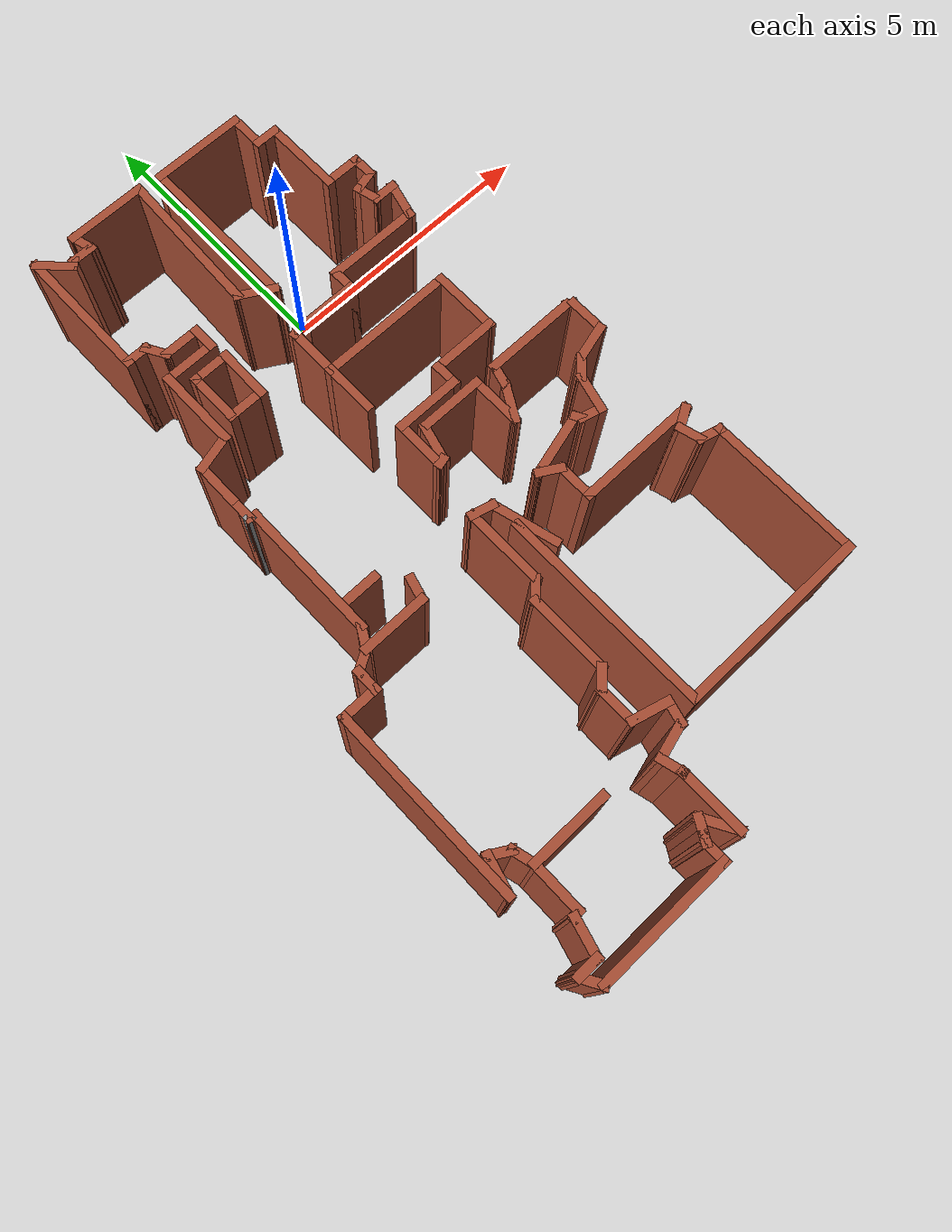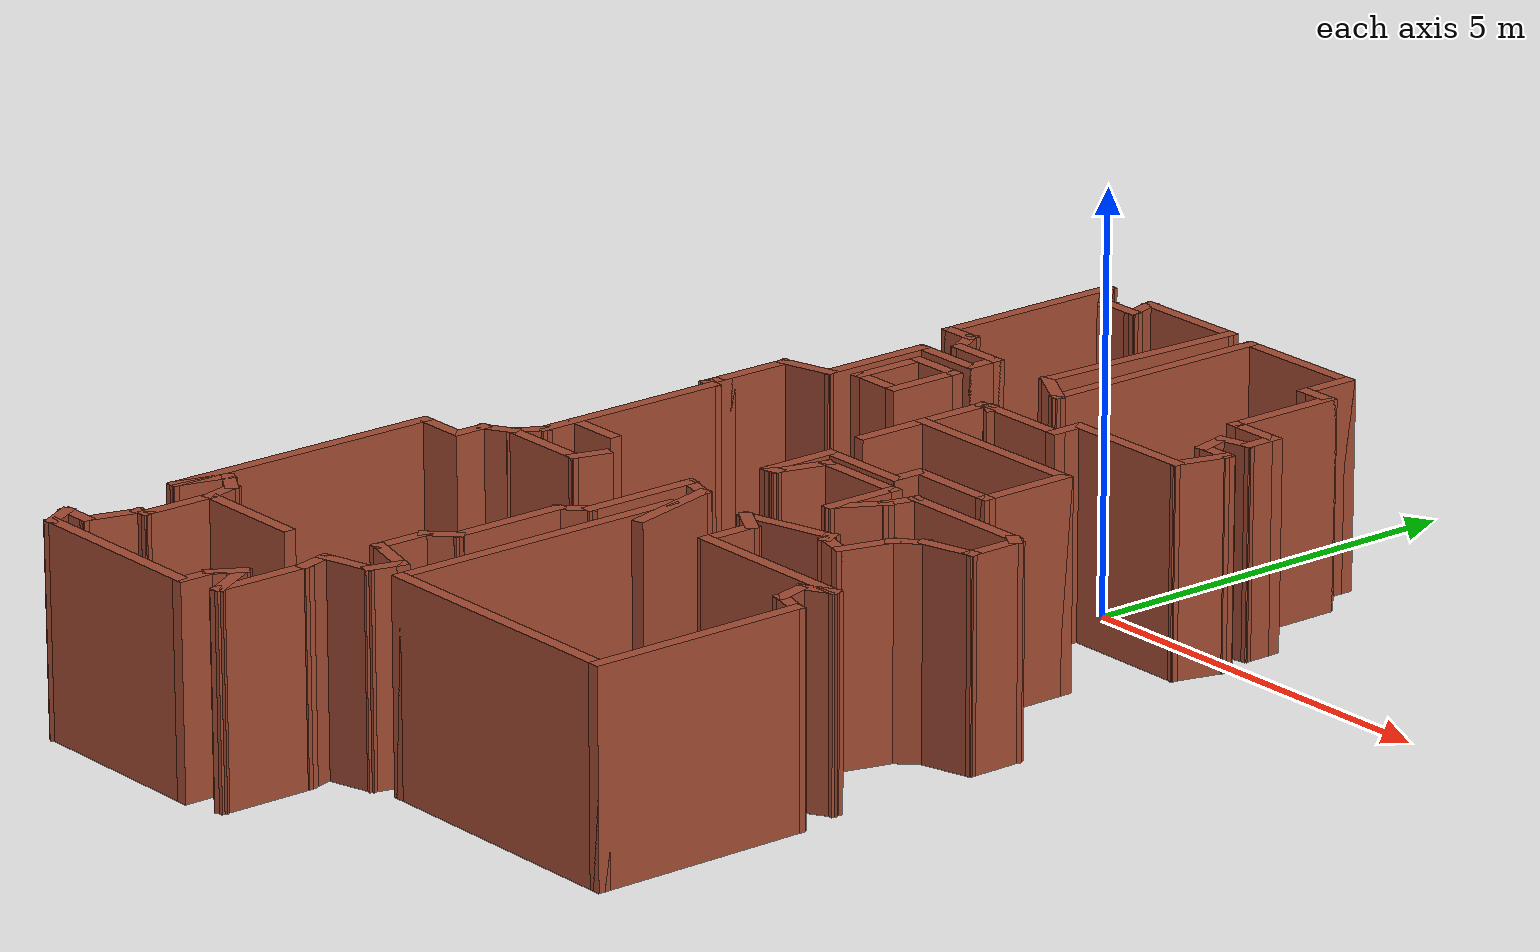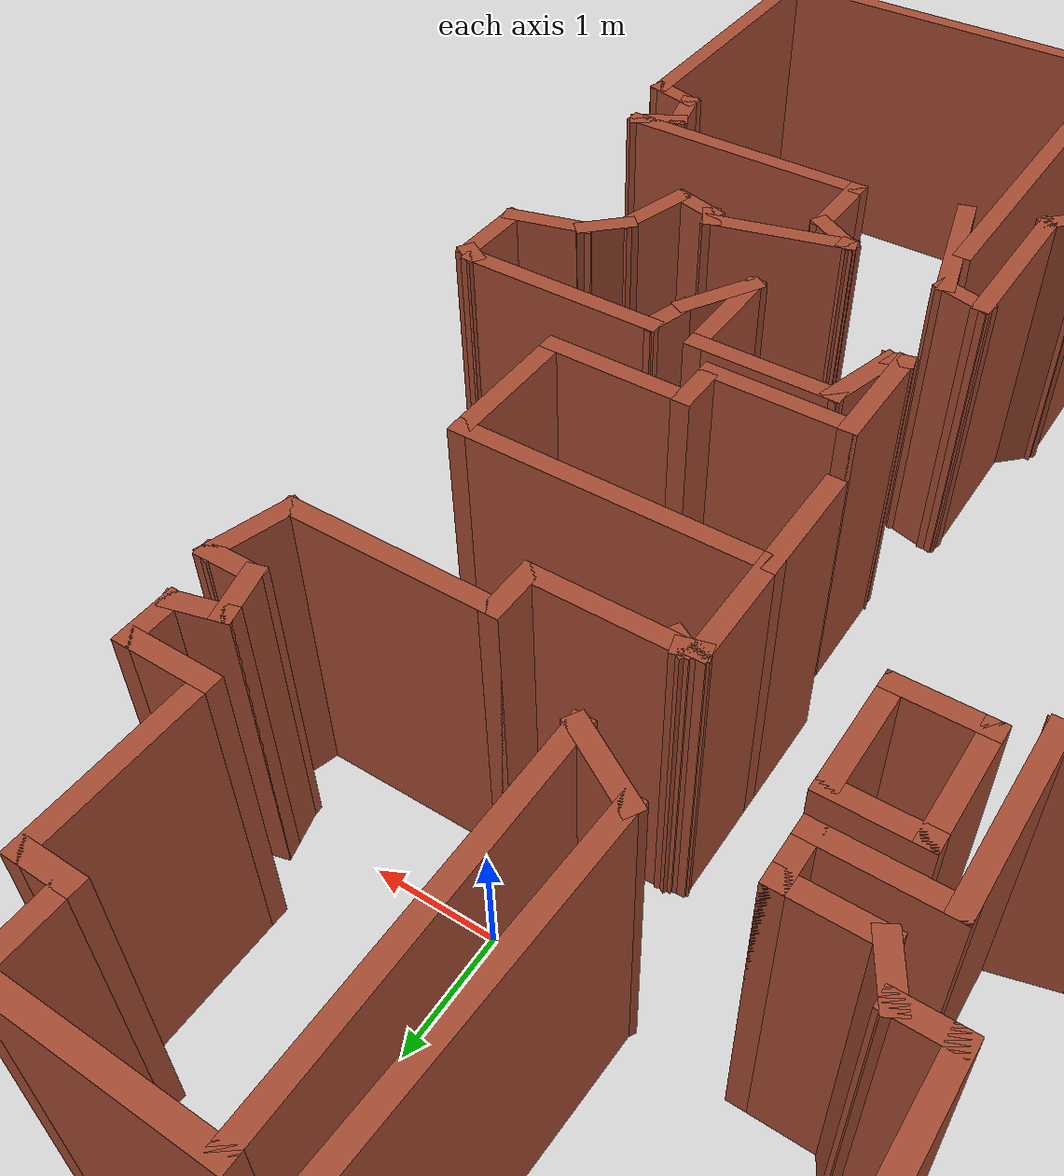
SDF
<?xml version='1.0'?>
<sdf version='1.6'>
  <model name='map_10'>
    <pose frame=''>-0.789034 -4.23581 0 0 -0 0</pose>
    <link name='Wall_0'>
      <collision name='Wall_0_Collision'>
        <geometry>
          <box>
            <size>1.5 0.15 2.5</size>
          </box>
        </geometry>
        <pose frame=''>0 0 1.25 0 -0 0</pose>
      </collision>
      <visual name='Wall_0_Visual'>
        <pose frame=''>0 0 1.25 0 -0 0</pose>
        <geometry>
          <box>
            <size>1.5 0.15 2.5</size>
          </box>
        </geometry>
        <material>
          <script>
            <uri>file://media/materials/scripts/gazebo.material</uri>
            <name>Gazebo/Bricks</name>
          </script>
          <ambient>1 1 1 1</ambient>
        </material>
        <meta>
          <layer>0</layer>
        </meta>
      </visual>
      <pose frame=''>-0.842764 6.90994 0 0 -0 3.14159</pose>
    </link>
    <link name='Wall_1'>
      <collision name='Wall_1_Collision'>
        <geometry>
          <box>
            <size>0.5 0.15 2.5</size>
          </box>
        </geometry>
        <pose frame=''>0 0 1.25 0 -0 0</pose>
      </collision>
      <visual name='Wall_1_Visual'>
        <pose frame=''>0 0 1.25 0 -0 0</pose>
        <geometry>
          <box>
            <size>0.5 0.15 2.5</size>
          </box>
        </geometry>
        <material>
          <script>
            <uri>file://media/materials/scripts/gazebo.material</uri>
            <name>Gazebo/Bricks</name>
          </script>
          <ambient>1 1 1 1</ambient>
        </material>
        <meta>
          <layer>0</layer>
        </meta>
      </visual>
      <pose frame=''>-1.47247 6.7409 0 0 -0 -1.309</pose>
    </link>
    <link name='Wall_10'>
      <collision name='Wall_10_Collision'>
        <geometry>
          <box>
            <size>1 0.15 2.5</size>
          </box>
        </geometry>
        <pose frame=''>0 0 1.25 0 -0 0</pose>
      </collision>
      <visual name='Wall_10_Visual'>
        <pose frame=''>0 0 1.25 0 -0 0</pose>
        <geometry>
          <box>
            <size>1 0.15 2.5</size>
          </box>
        </geometry>
        <material>
          <script>
            <uri>file://media/materials/scripts/gazebo.material</uri>
            <name>Gazebo/Bricks</name>
          </script>
          <ambient>1 1 1 1</ambient>
        </material>
        <meta>
          <layer>0</layer>
        </meta>
      </visual>
      <pose frame=''>-1.57215 3.92231 0 0 -0 3.14159</pose>
    </link>
    <link name='Wall_100'>
      <collision name='Wall_100_Collision'>
        <geometry>
          <box>
            <size>1.25 0.15 2.5</size>
          </box>
        </geometry>
        <pose frame=''>0 0 1.25 0 -0 0</pose>
      </collision>
      <visual name='Wall_100_Visual'>
        <pose frame=''>0 0 1.25 0 -0 0</pose>
        <geometry>
          <box>
            <size>1.25 0.15 2.5</size>
          </box>
        </geometry>
        <material>
          <script>
            <uri>file://media/materials/scripts/gazebo.material</uri>
            <name>Gazebo/Bricks</name>
          </script>
          <ambient>1 1 1 1</ambient>
        </material>
        <meta>
          <layer>0</layer>
        </meta>
      </visual>
      <pose frame=''>2.29691 1.76891 0 0 -0 1.5708</pose>
    </link>
    <link name='Wall_103'>
      <collision name='Wall_103_Collision'>
        <geometry>
          <box>
            <size>2.5 0.15 2.5</size>
          </box>
        </geometry>
        <pose frame=''>0 0 1.25 0 -0 0</pose>
      </collision>
      <visual name='Wall_103_Visual'>
        <pose frame=''>0 0 1.25 0 -0 0</pose>
        <geometry>
          <box>
            <size>2.5 0.15 2.5</size>
          </box>
        </geometry>
        <material>
          <script>
            <uri>file://media/materials/scripts/gazebo.material</uri>
            <name>Gazebo/Bricks</name>
          </script>
          <ambient>1 1 1 1</ambient>
        </material>
        <meta>
          <layer>0</layer>
        </meta>
      </visual>
      <pose frame=''>1.12191 2.31891 0 0 -0 3.14159</pose>
    </link>
    <link name='Wall_104'>
      <collision name='Wall_104_Collision'>
        <geometry>
          <box>
            <size>1 0.15 2.5</size>
          </box>
        </geometry>
        <pose frame=''>0 0 1.25 0 -0 0</pose>
      </collision>
      <visual name='Wall_104_Visual'>
        <pose frame=''>0 0 1.25 0 -0 0</pose>
        <geometry>
          <box>
            <size>1 0.15 2.5</size>
          </box>
        </geometry>
        <material>
          <script>
            <uri>file://media/materials/scripts/gazebo.material</uri>
            <name>Gazebo/Bricks</name>
          </script>
          <ambient>1 1 1 1</ambient>
        </material>
        <meta>
          <layer>0</layer>
        </meta>
      </visual>
      <pose frame=''>-0.05309 2.74391 0 0 -0 1.5708</pose>
    </link>
    <link name='Wall_105'>
      <collision name='Wall_105_Collision'>
        <geometry>
          <box>
            <size>0.25 0.15 2.5</size>
          </box>
        </geometry>
        <pose frame=''>0 0 1.25 0 -0 0</pose>
      </collision>
      <visual name='Wall_105_Visual'>
        <pose frame=''>0 0 1.25 0 -0 0</pose>
        <geometry>
          <box>
            <size>0.25 0.15 2.5</size>
          </box>
        </geometry>
        <material>
          <script>
            <uri>file://media/materials/scripts/gazebo.material</uri>
            <name>Gazebo/Bricks</name>
          </script>
          <ambient>1 1 1 1</ambient>
        </material>
        <meta>
          <layer>0</layer>
        </meta>
      </visual>
      <pose frame=''>-0.004794 3.18185 0 0 -0 0.261799</pose>
    </link>
    <link name='Wall_106'>
      <collision name='Wall_106_Collision'>
        <geometry>
          <box>
            <size>0.25 0.15 2.5</size>
          </box>
        </geometry>
        <pose frame=''>0 0 1.25 0 -0 0</pose>
      </collision>
      <visual name='Wall_106_Visual'>
        <pose frame=''>0 0 1.25 0 -0 0</pose>
        <geometry>
          <box>
            <size>0.25 0.15 2.5</size>
          </box>
        </geometry>
        <material>
          <script>
            <uri>file://media/materials/scripts/gazebo.material</uri>
            <name>Gazebo/Bricks</name>
          </script>
          <ambient>1 1 1 1</ambient>
        </material>
        <meta>
          <layer>0</layer>
        </meta>
      </visual>
      <pose frame=''>0.086804 3.16979 0 0 -0 -0.523599</pose>
    </link>
    <link name='Wall_109'>
      <collision name='Wall_109_Collision'>
        <geometry>
          <box>
            <size>1.25 0.15 2.5</size>
          </box>
        </geometry>
        <pose frame=''>0 0 1.25 0 -0 0</pose>
      </collision>
      <visual name='Wall_109_Visual'>
        <pose frame=''>0 0 1.25 0 -0 0</pose>
        <geometry>
          <box>
            <size>1.25 0.15 2.5</size>
          </box>
        </geometry>
        <material>
          <script>
            <uri>file://media/materials/scripts/gazebo.material</uri>
            <name>Gazebo/Bricks</name>
          </script>
          <ambient>1 1 1 1</ambient>
        </material>
        <meta>
          <layer>0</layer>
        </meta>
      </visual>
      <pose frame=''>0.593503 3.19479 0 0 -0 0</pose>
    </link>
    <link name='Wall_11'>
      <collision name='Wall_11_Collision'>
        <geometry>
          <box>
            <size>1.5 0.15 2.5</size>
          </box>
        </geometry>
        <pose frame=''>0 0 1.25 0 -0 0</pose>
      </collision>
      <visual name='Wall_11_Visual'>
        <pose frame=''>0 0 1.25 0 -0 0</pose>
        <geometry>
          <box>
            <size>1.5 0.15 2.5</size>
          </box>
        </geometry>
        <material>
          <script>
            <uri>file://media/materials/scripts/gazebo.material</uri>
            <name>Gazebo/Bricks</name>
          </script>
          <ambient>1 1 1 1</ambient>
        </material>
        <meta>
          <layer>0</layer>
        </meta>
      </visual>
      <pose frame=''>-1.99715 3.24731 0 0 -0 -1.5708</pose>
    </link>
    <link name='Wall_110'>
      <collision name='Wall_110_Collision'>
        <geometry>
          <box>
            <size>0.5 0.15 2.5</size>
          </box>
        </geometry>
        <pose frame=''>0 0 1.25 0 -0 0</pose>
      </collision>
      <visual name='Wall_110_Visual'>
        <pose frame=''>0 0 1.25 0 -0 0</pose>
        <geometry>
          <box>
            <size>0.5 0.15 2.5</size>
          </box>
        </geometry>
        <material>
          <script>
            <uri>file://media/materials/scripts/gazebo.material</uri>
            <name>Gazebo/Bricks</name>
          </script>
          <ambient>1 1 1 1</ambient>
        </material>
        <meta>
          <layer>0</layer>
        </meta>
      </visual>
      <pose frame=''>1.1435 3.36979 0 0 -0 1.5708</pose>
    </link>
    <link name='Wall_111'>
      <collision name='Wall_111_Collision'>
        <geometry>
          <box>
            <size>1.75 0.15 2.5</size>
          </box>
        </geometry>
        <pose frame=''>0 0 1.25 0 -0 0</pose>
      </collision>
      <visual name='Wall_111_Visual'>
        <pose frame=''>0 0 1.25 0 -0 0</pose>
        <geometry>
          <box>
            <size>1.75 0.15 2.5</size>
          </box>
        </geometry>
        <material>
          <script>
            <uri>file://media/materials/scripts/gazebo.material</uri>
            <name>Gazebo/Bricks</name>
          </script>
          <ambient>1 1 1 1</ambient>
        </material>
        <meta>
          <layer>0</layer>
        </meta>
      </visual>
      <pose frame=''>1.9435 3.54479 0 0 -0 0</pose>
    </link>
    <link name='Wall_112'>
      <collision name='Wall_112_Collision'>
        <geometry>
          <box>
            <size>0.75 0.15 2.5</size>
          </box>
        </geometry>
        <pose frame=''>0 0 1.25 0 -0 0</pose>
      </collision>
      <visual name='Wall_112_Visual'>
        <pose frame=''>0 0 1.25 0 -0 0</pose>
        <geometry>
          <box>
            <size>0.75 0.15 2.5</size>
          </box>
        </geometry>
        <material>
          <script>
            <uri>file://media/materials/scripts/gazebo.material</uri>
            <name>Gazebo/Bricks</name>
          </script>
          <ambient>1 1 1 1</ambient>
        </material>
        <meta>
          <layer>0</layer>
        </meta>
      </visual>
      <pose frame=''>2.82115 3.83457 0 0 -0 1.309</pose>
    </link>
    <link name='Wall_113'>
      <collision name='Wall_113_Collision'>
        <geometry>
          <box>
            <size>0.5 0.15 2.5</size>
          </box>
        </geometry>
        <pose frame=''>0 0 1.25 0 -0 0</pose>
      </collision>
      <visual name='Wall_113_Visual'>
        <pose frame=''>0 0 1.25 0 -0 0</pose>
        <geometry>
          <box>
            <size>0.5 0.15 2.5</size>
          </box>
        </geometry>
        <material>
          <script>
            <uri>file://media/materials/scripts/gazebo.material</uri>
            <name>Gazebo/Bricks</name>
          </script>
          <ambient>1 1 1 1</ambient>
        </material>
        <meta>
          <layer>0</layer>
        </meta>
      </visual>
      <pose frame=''>2.72379 4.12435 0 0 -0 3.14159</pose>
    </link>
    <link name='Wall_114'>
      <collision name='Wall_114_Collision'>
        <geometry>
          <box>
            <size>0.5 0.15 2.5</size>
          </box>
        </geometry>
        <pose frame=''>0 0 1.25 0 -0 0</pose>
      </collision>
      <visual name='Wall_114_Visual'>
        <pose frame=''>0 0 1.25 0 -0 0</pose>
        <geometry>
          <box>
            <size>0.5 0.15 2.5</size>
          </box>
        </geometry>
        <material>
          <script>
            <uri>file://media/materials/scripts/gazebo.material</uri>
            <name>Gazebo/Bricks</name>
          </script>
          <ambient>1 1 1 1</ambient>
        </material>
        <meta>
          <layer>0</layer>
        </meta>
      </visual>
      <pose frame=''>2.5035 4.29338 0 0 -0 1.8326</pose>
    </link>
    <link name='Wall_115'>
      <collision name='Wall_115_Collision'>
        <geometry>
          <box>
            <size>0.5 0.15 2.5</size>
          </box>
        </geometry>
        <pose frame=''>0 0 1.25 0 -0 0</pose>
      </collision>
      <visual name='Wall_115_Visual'>
        <pose frame=''>0 0 1.25 0 -0 0</pose>
        <geometry>
          <box>
            <size>0.5 0.15 2.5</size>
          </box>
        </geometry>
        <material>
          <script>
            <uri>file://media/materials/scripts/gazebo.material</uri>
            <name>Gazebo/Bricks</name>
          </script>
          <ambient>1 1 1 1</ambient>
        </material>
        <meta>
          <layer>0</layer>
        </meta>
      </visual>
      <pose frame=''>2.62724 4.50772 0 0 -0 0.261799</pose>
    </link>
    <link name='Wall_116'>
      <collision name='Wall_116_Collision'>
        <geometry>
          <box>
            <size>0.5 0.15 2.5</size>
          </box>
        </geometry>
        <pose frame=''>0 0 1.25 0 -0 0</pose>
      </collision>
      <visual name='Wall_116_Visual'>
        <pose frame=''>0 0 1.25 0 -0 0</pose>
        <geometry>
          <box>
            <size>0.5 0.15 2.5</size>
          </box>
        </geometry>
        <material>
          <script>
            <uri>file://media/materials/scripts/gazebo.material</uri>
            <name>Gazebo/Bricks</name>
          </script>
          <ambient>1 1 1 1</ambient>
        </material>
        <meta>
          <layer>0</layer>
        </meta>
      </visual>
      <pose frame=''>2.79628 4.72801 0 0 -0 1.5708</pose>
    </link>
    <link name='Wall_117'>
      <collision name='Wall_117_Collision'>
        <geometry>
          <box>
            <size>0.75 0.15 2.5</size>
          </box>
        </geometry>
        <pose frame=''>0 0 1.25 0 -0 0</pose>
      </collision>
      <visual name='Wall_117_Visual'>
        <pose frame=''>0 0 1.25 0 -0 0</pose>
        <geometry>
          <box>
            <size>0.75 0.15 2.5</size>
          </box>
        </geometry>
        <material>
          <script>
            <uri>file://media/materials/scripts/gazebo.material</uri>
            <name>Gazebo/Bricks</name>
          </script>
          <ambient>1 1 1 1</ambient>
        </material>
        <meta>
          <layer>0</layer>
        </meta>
      </visual>
      <pose frame=''>2.49628 4.90301 0 0 -0 3.14159</pose>
    </link>
    <link name='Wall_118'>
      <collision name='Wall_118_Collision'>
        <geometry>
          <box>
            <size>1.5 0.15 2.5</size>
          </box>
        </geometry>
        <pose frame=''>0 0 1.25 0 -0 0</pose>
      </collision>
      <visual name='Wall_118_Visual'>
        <pose frame=''>0 0 1.25 0 -0 0</pose>
        <geometry>
          <box>
            <size>1.5 0.15 2.5</size>
          </box>
        </geometry>
        <material>
          <script>
            <uri>file://media/materials/scripts/gazebo.material</uri>
            <name>Gazebo/Bricks</name>
          </script>
          <ambient>1 1 1 1</ambient>
        </material>
        <meta>
          <layer>0</layer>
        </meta>
      </visual>
      <pose frame=''>2.19628 5.57801 0 0 -0 1.5708</pose>
    </link>
    <link name='Wall_119'>
      <collision name='Wall_119_Collision'>
        <geometry>
          <box>
            <size>0.5 0.15 2.5</size>
          </box>
        </geometry>
        <pose frame=''>0 0 1.25 0 -0 0</pose>
      </collision>
      <visual name='Wall_119_Visual'>
        <pose frame=''>0 0 1.25 0 -0 0</pose>
        <geometry>
          <box>
            <size>0.5 0.15 2.5</size>
          </box>
        </geometry>
        <material>
          <script>
            <uri>file://media/materials/scripts/gazebo.material</uri>
            <name>Gazebo/Bricks</name>
          </script>
          <ambient>1 1 1 1</ambient>
        </material>
        <meta>
          <layer>0</layer>
        </meta>
      </visual>
      <pose frame=''>2.02128 6.25301 0 0 -0 3.14159</pose>
    </link>
    <link name='Wall_12'>
      <collision name='Wall_12_Collision'>
        <geometry>
          <box>
            <size>0.75 0.15 2.5</size>
          </box>
        </geometry>
        <pose frame=''>0 0 1.25 0 -0 0</pose>
      </collision>
      <visual name='Wall_12_Visual'>
        <pose frame=''>0 0 1.25 0 -0 0</pose>
        <geometry>
          <box>
            <size>0.75 0.15 2.5</size>
          </box>
        </geometry>
        <material>
          <script>
            <uri>file://media/materials/scripts/gazebo.material</uri>
            <name>Gazebo/Bricks</name>
          </script>
          <ambient>1 1 1 1</ambient>
        </material>
        <meta>
          <layer>0</layer>
        </meta>
      </visual>
      <pose frame=''>-2.28693 2.49467 0 0 -0 -2.87979</pose>
    </link>
    <link name='Wall_120'>
      <collision name='Wall_120_Collision'>
        <geometry>
          <box>
            <size>0.75 0.15 2.5</size>
          </box>
        </geometry>
        <pose frame=''>0 0 1.25 0 -0 0</pose>
      </collision>
      <visual name='Wall_120_Visual'>
        <pose frame=''>0 0 1.25 0 -0 0</pose>
        <geometry>
          <box>
            <size>0.75 0.15 2.5</size>
          </box>
        </geometry>
        <material>
          <script>
            <uri>file://media/materials/scripts/gazebo.material</uri>
            <name>Gazebo/Bricks</name>
          </script>
          <ambient>1 1 1 1</ambient>
        </material>
        <meta>
          <layer>0</layer>
        </meta>
      </visual>
      <pose frame=''>1.84628 6.55301 0 0 -0 1.5708</pose>
    </link>
    <link name='Wall_121'>
      <collision name='Wall_121_Collision'>
        <geometry>
          <box>
            <size>1.75 0.15 2.5</size>
          </box>
        </geometry>
        <pose frame=''>0 0 1.25 0 -0 0</pose>
      </collision>
      <visual name='Wall_121_Visual'>
        <pose frame=''>0 0 1.25 0 -0 0</pose>
        <geometry>
          <box>
            <size>1.75 0.15 2.5</size>
          </box>
        </geometry>
        <material>
          <script>
            <uri>file://media/materials/scripts/gazebo.material</uri>
            <name>Gazebo/Bricks</name>
          </script>
          <ambient>1 1 1 1</ambient>
        </material>
        <meta>
          <layer>0</layer>
        </meta>
      </visual>
      <pose frame=''>1.04628 6.85301 0 0 -0 3.14159</pose>
    </link>
    <link name='Wall_122'>
      <collision name='Wall_122_Collision'>
        <geometry>
          <box>
            <size>3 0.15 2.5</size>
          </box>
        </geometry>
        <pose frame=''>0 0 1.25 0 -0 0</pose>
      </collision>
      <visual name='Wall_122_Visual'>
        <pose frame=''>0 0 1.25 0 -0 0</pose>
        <geometry>
          <box>
            <size>3 0.15 2.5</size>
          </box>
        </geometry>
        <material>
          <script>
            <uri>file://media/materials/scripts/gazebo.material</uri>
            <name>Gazebo/Bricks</name>
          </script>
          <ambient>1 1 1 1</ambient>
        </material>
        <meta>
          <layer>0</layer>
        </meta>
      </visual>
      <pose frame=''>0.246282 5.42801 0 0 -0 -1.5708</pose>
    </link>
    <link name='Wall_123'>
      <collision name='Wall_123_Collision'>
        <geometry>
          <box>
            <size>0.75 0.15 2.5</size>
          </box>
        </geometry>
        <pose frame=''>0 0 1.25 0 -0 0</pose>
      </collision>
      <visual name='Wall_123_Visual'>
        <pose frame=''>0 0 1.25 0 -0 0</pose>
        <geometry>
          <box>
            <size>0.75 0.15 2.5</size>
          </box>
        </geometry>
        <material>
          <script>
            <uri>file://media/materials/scripts/gazebo.material</uri>
            <name>Gazebo/Bricks</name>
          </script>
          <ambient>1 1 1 1</ambient>
        </material>
        <meta>
          <layer>0</layer>
        </meta>
      </visual>
      <pose frame=''>-0.013526 4.15301 0 0 -0 2.61799</pose>
    </link>
    <link name='Wall_124'>
      <collision name='Wall_124_Collision'>
        <geometry>
          <box>
            <size>2.75907 0.15 2.5</size>
          </box>
        </geometry>
        <pose frame=''>0 0 1.25 0 -0 0</pose>
      </collision>
      <visual name='Wall_124_Visual'>
        <pose frame=''>0 0 1.25 0 -0 0</pose>
        <geometry>
          <box>
            <size>2.75907 0.15 2.5</size>
          </box>
        </geometry>
        <material>
          <script>
            <uri>file://media/materials/scripts/gazebo.material</uri>
            <name>Gazebo/Bricks</name>
          </script>
          <ambient>1 1 1 1</ambient>
        </material>
        <meta>
          <layer>0</layer>
        </meta>
      </visual>
      <pose frame=''>-0.220549 5.60647 0 0 -0 1.53032</pose>
    </link>
    <link name='Wall_126'>
      <collision name='Wall_126_Collision'>
        <geometry>
          <box>
            <size>1 0.15 2.5</size>
          </box>
        </geometry>
        <pose frame=''>0 0 1.25 0 -0 0</pose>
      </collision>
      <visual name='Wall_126_Visual'>
        <pose frame=''>0 0 1.25 0 -0 0</pose>
        <geometry>
          <box>
            <size>1 0.15 2.5</size>
          </box>
        </geometry>
        <material>
          <script>
            <uri>file://media/materials/scripts/gazebo.material</uri>
            <name>Gazebo/Bricks</name>
          </script>
          <ambient>1 1 1 1</ambient>
        </material>
        <meta>
          <layer>0</layer>
        </meta>
      </visual>
      <pose frame=''>-1.69438 3.20039 0 0 -0 -1.5708</pose>
    </link>
    <link name='Wall_127'>
      <collision name='Wall_127_Collision'>
        <geometry>
          <box>
            <size>0.75 0.15 2.5</size>
          </box>
        </geometry>
        <pose frame=''>0 0 1.25 0 -0 0</pose>
      </collision>
      <visual name='Wall_127_Visual'>
        <pose frame=''>0 0 1.25 0 -0 0</pose>
        <geometry>
          <box>
            <size>0.75 0.15 2.5</size>
          </box>
        </geometry>
        <material>
          <script>
            <uri>file://media/materials/scripts/gazebo.material</uri>
            <name>Gazebo/Bricks</name>
          </script>
          <ambient>1 1 1 1</ambient>
        </material>
        <meta>
          <layer>0</layer>
        </meta>
      </visual>
      <pose frame=''>-1.39438 2.7754 0 0 -0 0</pose>
    </link>
    <link name='Wall_130'>
      <collision name='Wall_130_Collision'>
        <geometry>
          <box>
            <size>1 0.15 2.5</size>
          </box>
        </geometry>
        <pose frame=''>0 0 1.25 0 -0 0</pose>
      </collision>
      <visual name='Wall_130_Visual'>
        <pose frame=''>0 0 1.25 0 -0 0</pose>
        <geometry>
          <box>
            <size>1 0.15 2.5</size>
          </box>
        </geometry>
        <material>
          <script>
            <uri>file://media/materials/scripts/gazebo.material</uri>
            <name>Gazebo/Bricks</name>
          </script>
          <ambient>1 1 1 1</ambient>
        </material>
        <meta>
          <layer>0</layer>
        </meta>
      </visual>
      <pose frame=''>-1.09438 3.20039 0 0 -0 1.5708</pose>
    </link>
    <link name='Wall_131'>
      <collision name='Wall_131_Collision'>
        <geometry>
          <box>
            <size>0.75 0.15 2.5</size>
          </box>
        </geometry>
        <pose frame=''>0 0 1.25 0 -0 0</pose>
      </collision>
      <visual name='Wall_131_Visual'>
        <pose frame=''>0 0 1.25 0 -0 0</pose>
        <geometry>
          <box>
            <size>0.75 0.15 2.5</size>
          </box>
        </geometry>
        <material>
          <script>
            <uri>file://media/materials/scripts/gazebo.material</uri>
            <name>Gazebo/Bricks</name>
          </script>
          <ambient>1 1 1 1</ambient>
        </material>
        <meta>
          <layer>0</layer>
        </meta>
      </visual>
      <pose frame=''>-1.39438 3.6254 0 0 -0 3.14159</pose>
    </link>
    <link name='Wall_133'>
      <collision name='Wall_133_Collision'>
        <geometry>
          <box>
            <size>0.75 0.15 2.5</size>
          </box>
        </geometry>
        <pose frame=''>0 0 1.25 0 -0 0</pose>
      </collision>
      <visual name='Wall_133_Visual'>
        <pose frame=''>0 0 1.25 0 -0 0</pose>
        <geometry>
          <box>
            <size>0.75 0.15 2.5</size>
          </box>
        </geometry>
        <material>
          <script>
            <uri>file://media/materials/scripts/gazebo.material</uri>
            <name>Gazebo/Bricks</name>
          </script>
          <ambient>1 1 1 1</ambient>
        </material>
        <meta>
          <layer>0</layer>
        </meta>
      </visual>
      <pose frame=''>-2.13456 -0.630637 0 0 -0 0</pose>
    </link>
    <link name='Wall_135'>
      <collision name='Wall_135_Collision'>
        <geometry>
          <box>
            <size>1 0.15 2.5</size>
          </box>
        </geometry>
        <pose frame=''>0 0 1.25 0 -0 0</pose>
      </collision>
      <visual name='Wall_135_Visual'>
        <pose frame=''>0 0 1.25 0 -0 0</pose>
        <geometry>
          <box>
            <size>1 0.15 2.5</size>
          </box>
        </geometry>
        <material>
          <script>
            <uri>file://media/materials/scripts/gazebo.material</uri>
            <name>Gazebo/Bricks</name>
          </script>
          <ambient>1 1 1 1</ambient>
        </material>
        <meta>
          <layer>0</layer>
        </meta>
      </visual>
      <pose frame=''>-0.05309 1.89391 0 0 -0 -1.5708</pose>
    </link>
    <link name='Wall_138'>
      <collision name='Wall_138_Collision'>
        <geometry>
          <box>
            <size>1.25 0.15 2.5</size>
          </box>
        </geometry>
        <pose frame=''>0 0 1.25 0 -0 0</pose>
      </collision>
      <visual name='Wall_138_Visual'>
        <pose frame=''>0 0 1.25 0 -0 0</pose>
        <geometry>
          <box>
            <size>1.25 0.15 2.5</size>
          </box>
        </geometry>
        <material>
          <script>
            <uri>file://media/materials/scripts/gazebo.material</uri>
            <name>Gazebo/Bricks</name>
          </script>
          <ambient>1 1 1 1</ambient>
        </material>
        <meta>
          <layer>0</layer>
        </meta>
      </visual>
      <pose frame=''>-2.10512 -1.36197 0 0 -0 0</pose>
    </link>
    <link name='Wall_139'>
      <collision name='Wall_139_Collision'>
        <geometry>
          <box>
            <size>0.5 0.15 2.5</size>
          </box>
        </geometry>
        <pose frame=''>0 0 1.25 0 -0 0</pose>
      </collision>
      <visual name='Wall_139_Visual'>
        <pose frame=''>0 0 1.25 0 -0 0</pose>
        <geometry>
          <box>
            <size>0.5 0.15 2.5</size>
          </box>
        </geometry>
        <material>
          <script>
            <uri>file://media/materials/scripts/gazebo.material</uri>
            <name>Gazebo/Bricks</name>
          </script>
          <ambient>1 1 1 1</ambient>
        </material>
        <meta>
          <layer>0</layer>
        </meta>
      </visual>
      <pose frame=''>-1.50982 -1.19293 0 0 -0 1.309</pose>
    </link>
    <link name='Wall_143'>
      <collision name='Wall_143_Collision'>
        <geometry>
          <box>
            <size>1.5 0.15 2.5</size>
          </box>
        </geometry>
        <pose frame=''>0 0 1.25 0 -0 0</pose>
      </collision>
      <visual name='Wall_143_Visual'>
        <pose frame=''>0 0 1.25 0 -0 0</pose>
        <geometry>
          <box>
            <size>1.5 0.15 2.5</size>
          </box>
        </geometry>
        <material>
          <script>
            <uri>file://media/materials/scripts/gazebo.material</uri>
            <name>Gazebo/Bricks</name>
          </script>
          <ambient>1 1 1 1</ambient>
        </material>
        <meta>
          <layer>0</layer>
        </meta>
      </visual>
      <pose frame=''>-2.33424 -5.17049 0 0 -0 0</pose>
    </link>
    <link name='Wall_18'>
      <collision name='Wall_18_Collision'>
        <geometry>
          <box>
            <size>0.15 0.15 2.5</size>
          </box>
        </geometry>
        <pose frame=''>0 0 1.25 0 -0 0</pose>
      </collision>
      <visual name='Wall_18_Visual'>
        <pose frame=''>0 0 1.25 0 -0 0</pose>
        <geometry>
          <box>
            <size>0.15 0.15 2.5</size>
          </box>
        </geometry>
        <material>
          <script>
            <uri>file://media/materials/scripts/gazebo.material</uri>
            <name>Gazebo/Grey</name>
          </script>
          <ambient>1 1 1 1</ambient>
        </material>
        <meta>
          <layer>0</layer>
        </meta>
      </visual>
      <pose frame=''>-2.57671 1.31702 0 0 -0 0</pose>
    </link>
    <link name='Wall_2'>
      <collision name='Wall_2_Collision'>
        <geometry>
          <box>
            <size>0.5 0.15 2.5</size>
          </box>
        </geometry>
        <pose frame=''>0 0 1.25 0 -0 0</pose>
      </collision>
      <visual name='Wall_2_Visual'>
        <pose frame=''>0 0 1.25 0 -0 0</pose>
        <geometry>
          <box>
            <size>0.5 0.15 2.5</size>
          </box>
        </geometry>
        <material>
          <script>
            <uri>file://media/materials/scripts/gazebo.material</uri>
            <name>Gazebo/Bricks</name>
          </script>
          <ambient>1 1 1 1</ambient>
        </material>
        <meta>
          <layer>0</layer>
        </meta>
      </visual>
      <pose frame=''>-1.60218 6.57187 0 0 -0 3.14159</pose>
    </link>
    <link name='Wall_20'>
      <collision name='Wall_20_Collision'>
        <geometry>
          <box>
            <size>1 0.15 2.5</size>
          </box>
        </geometry>
        <pose frame=''>0 0 1.25 0 -0 0</pose>
      </collision>
      <visual name='Wall_20_Visual'>
        <pose frame=''>0 0 1.25 0 -0 0</pose>
        <geometry>
          <box>
            <size>1 0.15 2.5</size>
          </box>
        </geometry>
        <material>
          <script>
            <uri>file://media/materials/scripts/gazebo.material</uri>
            <name>Gazebo/Bricks</name>
          </script>
          <ambient>1 1 1 1</ambient>
        </material>
        <meta>
          <layer>0</layer>
        </meta>
      </visual>
      <pose frame=''>-2.57671 1.99202 0 0 -0 -1.5708</pose>
    </link>
    <link name='Wall_21'>
      <collision name='Wall_21_Collision'>
        <geometry>
          <box>
            <size>0.4 0.15 2.5</size>
          </box>
        </geometry>
        <pose frame=''>0 0 1.25 0 -0 0</pose>
      </collision>
      <visual name='Wall_21_Visual'>
        <pose frame=''>0 0 1.25 0 -0 0</pose>
        <geometry>
          <box>
            <size>0.4 0.15 2.5</size>
          </box>
        </geometry>
        <material>
          <script>
            <uri>file://media/materials/scripts/gazebo.material</uri>
            <name>Gazebo/Bricks</name>
          </script>
          <ambient>1 1 1 1</ambient>
        </material>
        <meta>
          <layer>0</layer>
        </meta>
      </visual>
      <pose frame=''>-2.57671 1.44202 0 0 -0 -1.5708</pose>
    </link>
    <link name='Wall_27'>
      <collision name='Wall_27_Collision'>
        <geometry>
          <box>
            <size>0.15 0.15 2.5</size>
          </box>
        </geometry>
        <pose frame=''>0 0 1.25 0 -0 0</pose>
      </collision>
      <visual name='Wall_27_Visual'>
        <pose frame=''>0 0 1.25 0 -0 0</pose>
        <geometry>
          <box>
            <size>0.15 0.15 2.5</size>
          </box>
        </geometry>
        <material>
          <script>
            <uri>file://media/materials/scripts/gazebo.material</uri>
            <name>Gazebo/Bricks</name>
          </script>
          <ambient>1 1 1 1</ambient>
        </material>
        <meta>
          <layer>0</layer>
        </meta>
      </visual>
      <pose frame=''>-2.57671 1.31702 0 0 -0 0</pose>
    </link>
    <link name='Wall_29'>
      <collision name='Wall_29_Collision'>
        <geometry>
          <box>
            <size>0.25 0.15 2.5</size>
          </box>
        </geometry>
        <pose frame=''>0 0 1.25 0 -0 0</pose>
      </collision>
      <visual name='Wall_29_Visual'>
        <pose frame=''>0 0 1.25 0 -0 0</pose>
        <geometry>
          <box>
            <size>0.25 0.15 2.5</size>
          </box>
        </geometry>
        <material>
          <script>
            <uri>file://media/materials/scripts/gazebo.material</uri>
            <name>Gazebo/Bricks</name>
          </script>
          <ambient>1 1 1 1</ambient>
        </material>
        <meta>
          <layer>0</layer>
        </meta>
      </visual>
      <pose frame=''>-2.52841 1.30408 0 0 -0 -0.261799</pose>
    </link>
    <link name='Wall_3'>
      <collision name='Wall_3_Collision'>
        <geometry>
          <box>
            <size>0.25 0.15 2.5</size>
          </box>
        </geometry>
        <pose frame=''>0 0 1.25 0 -0 0</pose>
      </collision>
      <visual name='Wall_3_Visual'>
        <pose frame=''>0 0 1.25 0 -0 0</pose>
        <geometry>
          <box>
            <size>0.25 0.15 2.5</size>
          </box>
        </geometry>
        <material>
          <script>
            <uri>file://media/materials/scripts/gazebo.material</uri>
            <name>Gazebo/Bricks</name>
          </script>
          <ambient>1 1 1 1</ambient>
        </material>
        <meta>
          <layer>0</layer>
        </meta>
      </visual>
      <pose frame=''>-1.81253 6.53651 0 0 -0 -2.35619</pose>
    </link>
    <link name='Wall_30'>
      <collision name='Wall_30_Collision'>
        <geometry>
          <box>
            <size>2.5 0.15 2.5</size>
          </box>
        </geometry>
        <pose frame=''>0 0 1.25 0 -0 0</pose>
      </collision>
      <visual name='Wall_30_Visual'>
        <pose frame=''>0 0 1.25 0 -0 0</pose>
        <geometry>
          <box>
            <size>2.5 0.15 2.5</size>
          </box>
        </geometry>
        <material>
          <script>
            <uri>file://media/materials/scripts/gazebo.material</uri>
            <name>Gazebo/Bricks</name>
          </script>
          <ambient>1 1 1 1</ambient>
        </material>
        <meta>
          <layer>0</layer>
        </meta>
      </visual>
      <pose frame=''>-2.48012 0.116139 0 0 -0 -1.5708</pose>
    </link>
    <link name='Wall_31'>
      <collision name='Wall_31_Collision'>
        <geometry>
          <box>
            <size>0.5 0.15 2.5</size>
          </box>
        </geometry>
        <pose frame=''>0 0 1.25 0 -0 0</pose>
      </collision>
      <visual name='Wall_31_Visual'>
        <pose frame=''>0 0 1.25 0 -0 0</pose>
        <geometry>
          <box>
            <size>0.5 0.15 2.5</size>
          </box>
        </geometry>
        <material>
          <script>
            <uri>file://media/materials/scripts/gazebo.material</uri>
            <name>Gazebo/Bricks</name>
          </script>
          <ambient>1 1 1 1</ambient>
        </material>
        <meta>
          <layer>0</layer>
        </meta>
      </visual>
      <pose frame=''>-2.56761 -1.21042 0 0 -0 -2.0944</pose>
    </link>
    <link name='Wall_32'>
      <collision name='Wall_32_Collision'>
        <geometry>
          <box>
            <size>0.5 0.15 2.5</size>
          </box>
        </geometry>
        <pose frame=''>0 0 1.25 0 -0 0</pose>
      </collision>
      <visual name='Wall_32_Visual'>
        <pose frame=''>0 0 1.25 0 -0 0</pose>
        <geometry>
          <box>
            <size>0.5 0.15 2.5</size>
          </box>
        </geometry>
        <material>
          <script>
            <uri>file://media/materials/scripts/gazebo.material</uri>
            <name>Gazebo/Bricks</name>
          </script>
          <ambient>1 1 1 1</ambient>
        </material>
        <meta>
          <layer>0</layer>
        </meta>
      </visual>
      <pose frame=''>-2.80667 -1.44947 0 0 -0 -2.61799</pose>
    </link>
    <link name='Wall_33'>
      <collision name='Wall_33_Collision'>
        <geometry>
          <box>
            <size>0.5 0.15 2.5</size>
          </box>
        </geometry>
        <pose frame=''>0 0 1.25 0 -0 0</pose>
      </collision>
      <visual name='Wall_33_Visual'>
        <pose frame=''>0 0 1.25 0 -0 0</pose>
        <geometry>
          <box>
            <size>0.5 0.15 2.5</size>
          </box>
        </geometry>
        <material>
          <script>
            <uri>file://media/materials/scripts/gazebo.material</uri>
            <name>Gazebo/Bricks</name>
          </script>
          <ambient>1 1 1 1</ambient>
        </material>
        <meta>
          <layer>0</layer>
        </meta>
      </visual>
      <pose frame=''>-2.95822 -1.71197 0 0 -0 -1.5708</pose>
    </link>
    <link name='Wall_36'>
      <collision name='Wall_36_Collision'>
        <geometry>
          <box>
            <size>0.75 0.15 2.5</size>
          </box>
        </geometry>
        <pose frame=''>0 0 1.25 0 -0 0</pose>
      </collision>
      <visual name='Wall_36_Visual'>
        <pose frame=''>0 0 1.25 0 -0 0</pose>
        <geometry>
          <box>
            <size>0.75 0.15 2.5</size>
          </box>
        </geometry>
        <material>
          <script>
            <uri>file://media/materials/scripts/gazebo.material</uri>
            <name>Gazebo/Bricks</name>
          </script>
          <ambient>1 1 1 1</ambient>
        </material>
        <meta>
          <layer>0</layer>
        </meta>
      </visual>
      <pose frame=''>-3.25822 -1.88697 0 0 -0 3.14159</pose>
    </link>
    <link name='Wall_37'>
      <collision name='Wall_37_Collision'>
        <geometry>
          <box>
            <size>3.5 0.15 2.5</size>
          </box>
        </geometry>
        <pose frame=''>0 0 1.25 0 -0 0</pose>
      </collision>
      <visual name='Wall_37_Visual'>
        <pose frame=''>0 0 1.25 0 -0 0</pose>
        <geometry>
          <box>
            <size>3.5 0.15 2.5</size>
          </box>
        </geometry>
        <material>
          <script>
            <uri>file://media/materials/scripts/gazebo.material</uri>
            <name>Gazebo/Bricks</name>
          </script>
          <ambient>1 1 1 1</ambient>
        </material>
        <meta>
          <layer>0</layer>
        </meta>
      </visual>
      <pose frame=''>-3.55822 -3.56197 0 0 -0 -1.5708</pose>
    </link>
    <link name='Wall_38'>
      <collision name='Wall_38_Collision'>
        <geometry>
          <box>
            <size>0.75 0.15 2.5</size>
          </box>
        </geometry>
        <pose frame=''>0 0 1.25 0 -0 0</pose>
      </collision>
      <visual name='Wall_38_Visual'>
        <pose frame=''>0 0 1.25 0 -0 0</pose>
        <geometry>
          <box>
            <size>0.75 0.15 2.5</size>
          </box>
        </geometry>
        <material>
          <script>
            <uri>file://media/materials/scripts/gazebo.material</uri>
            <name>Gazebo/Bricks</name>
          </script>
          <ambient>1 1 1 1</ambient>
        </material>
        <meta>
          <layer>0</layer>
        </meta>
      </visual>
      <pose frame=''>-3.48058 -4.94719 0 0 -0 1.309</pose>
    </link>
    <link name='Wall_39'>
      <collision name='Wall_39_Collision'>
        <geometry>
          <box>
            <size>0.5 0.15 2.5</size>
          </box>
        </geometry>
        <pose frame=''>0 0 1.25 0 -0 0</pose>
      </collision>
      <visual name='Wall_39_Visual'>
        <pose frame=''>0 0 1.25 0 -0 0</pose>
        <geometry>
          <box>
            <size>0.5 0.15 2.5</size>
          </box>
        </geometry>
        <material>
          <script>
            <uri>file://media/materials/scripts/gazebo.material</uri>
            <name>Gazebo/Bricks</name>
          </script>
          <ambient>1 1 1 1</ambient>
        </material>
        <meta>
          <layer>0</layer>
        </meta>
      </visual>
      <pose frame=''>-3.25138 -4.74491 0 0 -0 -0.523599</pose>
    </link>
    <link name='Wall_4'>
      <collision name='Wall_4_Collision'>
        <geometry>
          <box>
            <size>0.75 0.15 2.5</size>
          </box>
        </geometry>
        <pose frame=''>0 0 1.25 0 -0 0</pose>
      </collision>
      <visual name='Wall_4_Visual'>
        <pose frame=''>0 0 1.25 0 -0 0</pose>
        <geometry>
          <box>
            <size>0.75 0.15 2.5</size>
          </box>
        </geometry>
        <material>
          <script>
            <uri>file://media/materials/scripts/gazebo.material</uri>
            <name>Gazebo/Bricks</name>
          </script>
          <ambient>1 1 1 1</ambient>
        </material>
        <meta>
          <layer>0</layer>
        </meta>
      </visual>
      <pose frame=''>-2.06002 6.71329 0 0 -0 2.35619</pose>
    </link>
    <link name='Wall_40'>
      <collision name='Wall_40_Collision'>
        <geometry>
          <box>
            <size>0.5 0.15 2.5</size>
          </box>
        </geometry>
        <pose frame=''>0 0 1.25 0 -0 0</pose>
      </collision>
      <visual name='Wall_40_Visual'>
        <pose frame=''>0 0 1.25 0 -0 0</pose>
        <geometry>
          <box>
            <size>0.5 0.15 2.5</size>
          </box>
        </geometry>
        <material>
          <script>
            <uri>file://media/materials/scripts/gazebo.material</uri>
            <name>Gazebo/Bricks</name>
          </script>
          <ambient>1 1 1 1</ambient>
        </material>
        <meta>
          <layer>0</layer>
        </meta>
      </visual>
      <pose frame=''>-3.05453 -5.00145 0 0 -0 -1.309</pose>
    </link>
    <link name='Wall_41'>
      <collision name='Wall_41_Collision'>
        <geometry>
          <box>
            <size>1 0.15 2.5</size>
          </box>
        </geometry>
        <pose frame=''>0 0 1.25 0 -0 0</pose>
      </collision>
      <visual name='Wall_41_Visual'>
        <pose frame=''>0 0 1.25 0 -0 0</pose>
        <geometry>
          <box>
            <size>1 0.15 2.5</size>
          </box>
        </geometry>
        <material>
          <script>
            <uri>file://media/materials/scripts/gazebo.material</uri>
            <name>Gazebo/Bricks</name>
          </script>
          <ambient>1 1 1 1</ambient>
        </material>
        <meta>
          <layer>0</layer>
        </meta>
      </visual>
      <pose frame=''>-3.00924 -5.59549 0 0 -0 -1.5708</pose>
    </link>
    <link name='Wall_44'>
      <collision name='Wall_44_Collision'>
        <geometry>
          <box>
            <size>0.25 0.15 2.5</size>
          </box>
        </geometry>
        <pose frame=''>0 0 1.25 0 -0 0</pose>
      </collision>
      <visual name='Wall_44_Visual'>
        <pose frame=''>0 0 1.25 0 -0 0</pose>
        <geometry>
          <box>
            <size>0.25 0.15 2.5</size>
          </box>
        </geometry>
        <material>
          <script>
            <uri>file://media/materials/scripts/gazebo.material</uri>
            <name>Gazebo/Bricks</name>
          </script>
          <ambient>1 1 1 1</ambient>
        </material>
        <meta>
          <layer>0</layer>
        </meta>
      </visual>
      <pose frame=''>-3.05753 -6.03343 0 0 -0 -2.87979</pose>
    </link>
    <link name='Wall_45'>
      <collision name='Wall_45_Collision'>
        <geometry>
          <box>
            <size>0.75 0.15 2.5</size>
          </box>
        </geometry>
        <pose frame=''>0 0 1.25 0 -0 0</pose>
      </collision>
      <visual name='Wall_45_Visual'>
        <pose frame=''>0 0 1.25 0 -0 0</pose>
        <geometry>
          <box>
            <size>0.75 0.15 2.5</size>
          </box>
        </geometry>
        <material>
          <script>
            <uri>file://media/materials/scripts/gazebo.material</uri>
            <name>Gazebo/Bricks</name>
          </script>
          <ambient>1 1 1 1</ambient>
        </material>
        <meta>
          <layer>0</layer>
        </meta>
      </visual>
      <pose frame=''>-3.18348 -6.33615 0 0 -0 -1.8326</pose>
    </link>
    <link name='Wall_46'>
      <collision name='Wall_46_Collision'>
        <geometry>
          <box>
            <size>0.5 0.15 2.5</size>
          </box>
        </geometry>
        <pose frame=''>0 0 1.25 0 -0 0</pose>
      </collision>
      <visual name='Wall_46_Visual'>
        <pose frame=''>0 0 1.25 0 -0 0</pose>
        <geometry>
          <box>
            <size>0.5 0.15 2.5</size>
          </box>
        </geometry>
        <material>
          <script>
            <uri>file://media/materials/scripts/gazebo.material</uri>
            <name>Gazebo/Bricks</name>
          </script>
          <ambient>1 1 1 1</ambient>
        </material>
        <meta>
          <layer>0</layer>
        </meta>
      </visual>
      <pose frame=''>-3.43612 -6.62593 0 0 -0 3.14159</pose>
    </link>
    <link name='Wall_47'>
      <collision name='Wall_47_Collision'>
        <geometry>
          <box>
            <size>0.5 0.15 2.5</size>
          </box>
        </geometry>
        <pose frame=''>0 0 1.25 0 -0 0</pose>
      </collision>
      <visual name='Wall_47_Visual'>
        <pose frame=''>0 0 1.25 0 -0 0</pose>
        <geometry>
          <box>
            <size>0.5 0.15 2.5</size>
          </box>
        </geometry>
        <material>
          <script>
            <uri>file://media/materials/scripts/gazebo.material</uri>
            <name>Gazebo/Bricks</name>
          </script>
          <ambient>1 1 1 1</ambient>
        </material>
        <meta>
          <layer>0</layer>
        </meta>
      </visual>
      <pose frame=''>-3.52362 -6.77748 0 0 -0 -1.0472</pose>
    </link>
    <link name='Wall_48'>
      <collision name='Wall_48_Collision'>
        <geometry>
          <box>
            <size>2.5 0.15 2.5</size>
          </box>
        </geometry>
        <pose frame=''>0 0 1.25 0 -0 0</pose>
      </collision>
      <visual name='Wall_48_Visual'>
        <pose frame=''>0 0 1.25 0 -0 0</pose>
        <geometry>
          <box>
            <size>2.5 0.15 2.5</size>
          </box>
        </geometry>
        <material>
          <script>
            <uri>file://media/materials/scripts/gazebo.material</uri>
            <name>Gazebo/Bricks</name>
          </script>
          <ambient>1 1 1 1</ambient>
        </material>
        <meta>
          <layer>0</layer>
        </meta>
      </visual>
      <pose frame=''>-2.26112 -6.92903 0 0 -0 0</pose>
    </link>
    <link name='Wall_49'>
      <collision name='Wall_49_Collision'>
        <geometry>
          <box>
            <size>0.5 0.15 2.5</size>
          </box>
        </geometry>
        <pose frame=''>0 0 1.25 0 -0 0</pose>
      </collision>
      <visual name='Wall_49_Visual'>
        <pose frame=''>0 0 1.25 0 -0 0</pose>
        <geometry>
          <box>
            <size>0.5 0.15 2.5</size>
          </box>
        </geometry>
        <material>
          <script>
            <uri>file://media/materials/scripts/gazebo.material</uri>
            <name>Gazebo/Bricks</name>
          </script>
          <ambient>1 1 1 1</ambient>
        </material>
        <meta>
          <layer>0</layer>
        </meta>
      </visual>
      <pose frame=''>-1.08612 -6.75404 0 0 -0 1.5708</pose>
    </link>
    <link name='Wall_5'>
      <collision name='Wall_5_Collision'>
        <geometry>
          <box>
            <size>2.5 0.15 2.5</size>
          </box>
        </geometry>
        <pose frame=''>0 0 1.25 0 -0 0</pose>
      </collision>
      <visual name='Wall_5_Visual'>
        <pose frame=''>0 0 1.25 0 -0 0</pose>
        <geometry>
          <box>
            <size>2.5 0.15 2.5</size>
          </box>
        </geometry>
        <material>
          <script>
            <uri>file://media/materials/scripts/gazebo.material</uri>
            <name>Gazebo/Bricks</name>
          </script>
          <ambient>1 1 1 1</ambient>
        </material>
        <meta>
          <layer>0</layer>
        </meta>
      </visual>
      <pose frame=''>-2.27215 5.75042 0 0 -0 -1.5708</pose>
    </link>
    <link name='Wall_50'>
      <collision name='Wall_50_Collision'>
        <geometry>
          <box>
            <size>0.25 0.15 2.5</size>
          </box>
        </geometry>
        <pose frame=''>0 0 1.25 0 -0 0</pose>
      </collision>
      <visual name='Wall_50_Visual'>
        <pose frame=''>0 0 1.25 0 -0 0</pose>
        <geometry>
          <box>
            <size>0.25 0.15 2.5</size>
          </box>
        </geometry>
        <material>
          <script>
            <uri>file://media/materials/scripts/gazebo.material</uri>
            <name>Gazebo/Bricks</name>
          </script>
          <ambient>1 1 1 1</ambient>
        </material>
        <meta>
          <layer>0</layer>
        </meta>
      </visual>
      <pose frame=''>-1.06112 -6.53573 0 0 -0 1.0472</pose>
    </link>
    <link name='Wall_53'>
      <collision name='Wall_53_Collision'>
        <geometry>
          <box>
            <size>0.5 0.15 2.5</size>
          </box>
        </geometry>
        <pose frame=''>0 0 1.25 0 -0 0</pose>
      </collision>
      <visual name='Wall_53_Visual'>
        <pose frame=''>0 0 1.25 0 -0 0</pose>
        <geometry>
          <box>
            <size>0.5 0.15 2.5</size>
          </box>
        </geometry>
        <material>
          <script>
            <uri>file://media/materials/scripts/gazebo.material</uri>
            <name>Gazebo/Bricks</name>
          </script>
          <ambient>1 1 1 1</ambient>
        </material>
        <meta>
          <layer>0</layer>
        </meta>
      </visual>
      <pose frame=''>-0.998621 -6.42748 0 0 -0 1.0472</pose>
    </link>
    <link name='Wall_54'>
      <collision name='Wall_54_Collision'>
        <geometry>
          <box>
            <size>0.75 0.15 2.5</size>
          </box>
        </geometry>
        <pose frame=''>0 0 1.25 0 -0 0</pose>
      </collision>
      <visual name='Wall_54_Visual'>
        <pose frame=''>0 0 1.25 0 -0 0</pose>
        <geometry>
          <box>
            <size>0.75 0.15 2.5</size>
          </box>
        </geometry>
        <material>
          <script>
            <uri>file://media/materials/scripts/gazebo.material</uri>
            <name>Gazebo/Bricks</name>
          </script>
          <ambient>1 1 1 1</ambient>
        </material>
        <meta>
          <layer>0</layer>
        </meta>
      </visual>
      <pose frame=''>-0.761121 -6.53573 0 0 -0 -1.0472</pose>
    </link>
    <link name='Wall_55'>
      <collision name='Wall_55_Collision'>
        <geometry>
          <box>
            <size>1.25 0.15 2.5</size>
          </box>
        </geometry>
        <pose frame=''>0 0 1.25 0 -0 0</pose>
      </collision>
      <visual name='Wall_55_Visual'>
        <pose frame=''>0 0 1.25 0 -0 0</pose>
        <geometry>
          <box>
            <size>1.25 0.15 2.5</size>
          </box>
        </geometry>
        <material>
          <script>
            <uri>file://media/materials/scripts/gazebo.material</uri>
            <name>Gazebo/Bricks</name>
          </script>
          <ambient>1 1 1 1</ambient>
        </material>
        <meta>
          <layer>0</layer>
        </meta>
      </visual>
      <pose frame=''>-0.611121 -6.24554 0 0 -0 1.5708</pose>
    </link>
    <link name='Wall_56'>
      <collision name='Wall_56_Collision'>
        <geometry>
          <box>
            <size>0.5 0.15 2.5</size>
          </box>
        </geometry>
        <pose frame=''>0 0 1.25 0 -0 0</pose>
      </collision>
      <visual name='Wall_56_Visual'>
        <pose frame=''>0 0 1.25 0 -0 0</pose>
        <geometry>
          <box>
            <size>0.5 0.15 2.5</size>
          </box>
        </geometry>
        <material>
          <script>
            <uri>file://media/materials/scripts/gazebo.material</uri>
            <name>Gazebo/Bricks</name>
          </script>
          <ambient>1 1 1 1</ambient>
        </material>
        <meta>
          <layer>0</layer>
        </meta>
      </visual>
      <pose frame=''>-0.656414 -5.5265 0 0 -0 1.8326</pose>
    </link>
    <link name='Wall_57'>
      <collision name='Wall_57_Collision'>
        <geometry>
          <box>
            <size>0.75 0.15 2.5</size>
          </box>
        </geometry>
        <pose frame=''>0 0 1.25 0 -0 0</pose>
      </collision>
      <visual name='Wall_57_Visual'>
        <pose frame=''>0 0 1.25 0 -0 0</pose>
        <geometry>
          <box>
            <size>0.75 0.15 2.5</size>
          </box>
        </geometry>
        <material>
          <script>
            <uri>file://media/materials/scripts/gazebo.material</uri>
            <name>Gazebo/Bricks</name>
          </script>
          <ambient>1 1 1 1</ambient>
        </material>
        <meta>
          <layer>0</layer>
        </meta>
      </visual>
      <pose frame=''>-0.41193 -5.27982 0 0 -0 0.261799</pose>
    </link>
    <link name='Wall_58'>
      <collision name='Wall_58_Collision'>
        <geometry>
          <box>
            <size>0.5 0.15 2.5</size>
          </box>
        </geometry>
        <pose frame=''>0 0 1.25 0 -0 0</pose>
      </collision>
      <visual name='Wall_58_Visual'>
        <pose frame=''>0 0 1.25 0 -0 0</pose>
        <geometry>
          <box>
            <size>0.5 0.15 2.5</size>
          </box>
        </geometry>
        <material>
          <script>
            <uri>file://media/materials/scripts/gazebo.material</uri>
            <name>Gazebo/Bricks</name>
          </script>
          <ambient>1 1 1 1</ambient>
        </material>
        <meta>
          <layer>0</layer>
        </meta>
      </visual>
      <pose frame=''>-0.076859 -5.03314 0 0 -0 1.309</pose>
    </link>
    <link name='Wall_59'>
      <collision name='Wall_59_Collision'>
        <geometry>
          <box>
            <size>0.75 0.15 2.5</size>
          </box>
        </geometry>
        <pose frame=''>0 0 1.25 0 -0 0</pose>
      </collision>
      <visual name='Wall_59_Visual'>
        <pose frame=''>0 0 1.25 0 -0 0</pose>
        <geometry>
          <box>
            <size>0.75 0.15 2.5</size>
          </box>
        </geometry>
        <material>
          <script>
            <uri>file://media/materials/scripts/gazebo.material</uri>
            <name>Gazebo/Bricks</name>
          </script>
          <ambient>1 1 1 1</ambient>
        </material>
        <meta>
          <layer>0</layer>
        </meta>
      </visual>
      <pose frame=''>-0.321343 -4.78646 0 0 -0 2.87979</pose>
    </link>
    <link name='Wall_6'>
      <collision name='Wall_6_Collision'>
        <geometry>
          <box>
            <size>0.5 0.15 2.5</size>
          </box>
        </geometry>
        <pose frame=''>0 0 1.25 0 -0 0</pose>
      </collision>
      <visual name='Wall_6_Visual'>
        <pose frame=''>0 0 1.25 0 -0 0</pose>
        <geometry>
          <box>
            <size>0.5 0.15 2.5</size>
          </box>
        </geometry>
        <material>
          <script>
            <uri>file://media/materials/scripts/gazebo.material</uri>
            <name>Gazebo/Bricks</name>
          </script>
          <ambient>1 1 1 1</ambient>
        </material>
        <meta>
          <layer>0</layer>
        </meta>
      </visual>
      <pose frame=''>-2.09715 4.57542 0 0 -0 0</pose>
    </link>
    <link name='Wall_60'>
      <collision name='Wall_60_Collision'>
        <geometry>
          <box>
            <size>0.75 0.15 2.5</size>
          </box>
        </geometry>
        <pose frame=''>0 0 1.25 0 -0 0</pose>
      </collision>
      <visual name='Wall_60_Visual'>
        <pose frame=''>0 0 1.25 0 -0 0</pose>
        <geometry>
          <box>
            <size>0.75 0.15 2.5</size>
          </box>
        </geometry>
        <material>
          <script>
            <uri>file://media/materials/scripts/gazebo.material</uri>
            <name>Gazebo/Bricks</name>
          </script>
          <ambient>1 1 1 1</ambient>
        </material>
        <meta>
          <layer>0</layer>
        </meta>
      </visual>
      <pose frame=''>-0.611121 -4.40881 0 0 -0 1.5708</pose>
    </link>
    <link name='Wall_61'>
      <collision name='Wall_61_Collision'>
        <geometry>
          <box>
            <size>0.5 0.15 2.5</size>
          </box>
        </geometry>
        <pose frame=''>0 0 1.25 0 -0 0</pose>
      </collision>
      <visual name='Wall_61_Visual'>
        <pose frame=''>0 0 1.25 0 -0 0</pose>
        <geometry>
          <box>
            <size>0.5 0.15 2.5</size>
          </box>
        </geometry>
        <material>
          <script>
            <uri>file://media/materials/scripts/gazebo.material</uri>
            <name>Gazebo/Bricks</name>
          </script>
          <ambient>1 1 1 1</ambient>
        </material>
        <meta>
          <layer>0</layer>
        </meta>
      </visual>
      <pose frame=''>-0.487377 -3.98507 0 0 -0 0.785398</pose>
    </link>
    <link name='Wall_62'>
      <collision name='Wall_62_Collision'>
        <geometry>
          <box>
            <size>1.5 0.15 2.5</size>
          </box>
        </geometry>
        <pose frame=''>0 0 1.25 0 -0 0</pose>
      </collision>
      <visual name='Wall_62_Visual'>
        <pose frame=''>0 0 1.25 0 -0 0</pose>
        <geometry>
          <box>
            <size>1.5 0.15 2.5</size>
          </box>
        </geometry>
        <material>
          <script>
            <uri>file://media/materials/scripts/gazebo.material</uri>
            <name>Gazebo/Bricks</name>
          </script>
          <ambient>1 1 1 1</ambient>
        </material>
        <meta>
          <layer>0</layer>
        </meta>
      </visual>
      <pose frame=''>-0.363634 -3.18632 0 0 -0 1.5708</pose>
    </link>
    <link name='Wall_63'>
      <collision name='Wall_63_Collision'>
        <geometry>
          <box>
            <size>0.5 0.15 2.5</size>
          </box>
        </geometry>
        <pose frame=''>0 0 1.25 0 -0 0</pose>
      </collision>
      <visual name='Wall_63_Visual'>
        <pose frame=''>0 0 1.25 0 -0 0</pose>
        <geometry>
          <box>
            <size>0.5 0.15 2.5</size>
          </box>
        </geometry>
        <material>
          <script>
            <uri>file://media/materials/scripts/gazebo.material</uri>
            <name>Gazebo/Bricks</name>
          </script>
          <ambient>1 1 1 1</ambient>
        </material>
        <meta>
          <layer>0</layer>
        </meta>
      </visual>
      <pose frame=''>-0.23989 -2.38758 0 0 -0 0.785398</pose>
    </link>
    <link name='Wall_64'>
      <collision name='Wall_64_Collision'>
        <geometry>
          <box>
            <size>1.5 0.15 2.5</size>
          </box>
        </geometry>
        <pose frame=''>0 0 1.25 0 -0 0</pose>
      </collision>
      <visual name='Wall_64_Visual'>
        <pose frame=''>0 0 1.25 0 -0 0</pose>
        <geometry>
          <box>
            <size>1.5 0.15 2.5</size>
          </box>
        </geometry>
        <material>
          <script>
            <uri>file://media/materials/scripts/gazebo.material</uri>
            <name>Gazebo/Bricks</name>
          </script>
          <ambient>1 1 1 1</ambient>
        </material>
        <meta>
          <layer>0</layer>
        </meta>
      </visual>
      <pose frame=''>-0.116146 -1.58884 0 0 -0 1.5708</pose>
    </link>
    <link name='Wall_65'>
      <collision name='Wall_65_Collision'>
        <geometry>
          <box>
            <size>0.5 0.15 2.5</size>
          </box>
        </geometry>
        <pose frame=''>0 0 1.25 0 -0 0</pose>
      </collision>
      <visual name='Wall_65_Visual'>
        <pose frame=''>0 0 1.25 0 -0 0</pose>
        <geometry>
          <box>
            <size>0.5 0.15 2.5</size>
          </box>
        </geometry>
        <material>
          <script>
            <uri>file://media/materials/scripts/gazebo.material</uri>
            <name>Gazebo/Bricks</name>
          </script>
          <ambient>1 1 1 1</ambient>
        </material>
        <meta>
          <layer>0</layer>
        </meta>
      </visual>
      <pose frame=''>0.052891 -0.959129 0 0 -0 -0.261799</pose>
    </link>
    <link name='Wall_66'>
      <collision name='Wall_66_Collision'>
        <geometry>
          <box>
            <size>1.25 0.15 2.5</size>
          </box>
        </geometry>
        <pose frame=''>0 0 1.25 0 -0 0</pose>
      </collision>
      <visual name='Wall_66_Visual'>
        <pose frame=''>0 0 1.25 0 -0 0</pose>
        <geometry>
          <box>
            <size>1.25 0.15 2.5</size>
          </box>
        </geometry>
        <material>
          <script>
            <uri>file://media/materials/scripts/gazebo.material</uri>
            <name>Gazebo/Bricks</name>
          </script>
          <ambient>1 1 1 1</ambient>
        </material>
        <meta>
          <layer>0</layer>
        </meta>
      </visual>
      <pose frame=''>0.364278 -1.53568 0 0 -0 -1.309</pose>
    </link>
    <link name='Wall_68'>
      <collision name='Wall_68_Collision'>
        <geometry>
          <box>
            <size>3.75 0.15 2.5</size>
          </box>
        </geometry>
        <pose frame=''>0 0 1.25 0 -0 0</pose>
      </collision>
      <visual name='Wall_68_Visual'>
        <pose frame=''>0 0 1.25 0 -0 0</pose>
        <geometry>
          <box>
            <size>3.75 0.15 2.5</size>
          </box>
        </geometry>
        <material>
          <script>
            <uri>file://media/materials/scripts/gazebo.material</uri>
            <name>Gazebo/Bricks</name>
          </script>
          <ambient>1 1 1 1</ambient>
        </material>
        <meta>
          <layer>0</layer>
        </meta>
      </visual>
      <pose frame=''>0.271717 -3.28647 0 0 -0 -1.5708</pose>
    </link>
    <link name='Wall_69'>
      <collision name='Wall_69_Collision'>
        <geometry>
          <box>
            <size>3.5 0.15 2.5</size>
          </box>
        </geometry>
        <pose frame=''>0 0 1.25 0 -0 0</pose>
      </collision>
      <visual name='Wall_69_Visual'>
        <pose frame=''>0 0 1.25 0 -0 0</pose>
        <geometry>
          <box>
            <size>3.5 0.15 2.5</size>
          </box>
        </geometry>
        <material>
          <script>
            <uri>file://media/materials/scripts/gazebo.material</uri>
            <name>Gazebo/Bricks</name>
          </script>
          <ambient>1 1 1 1</ambient>
        </material>
        <meta>
          <layer>0</layer>
        </meta>
      </visual>
      <pose frame=''>1.94672 -5.08647 0 0 -0 0</pose>
    </link>
    <link name='Wall_7'>
      <collision name='Wall_7_Collision'>
        <geometry>
          <box>
            <size>0.5 0.15 2.5</size>
          </box>
        </geometry>
        <pose frame=''>0 0 1.25 0 -0 0</pose>
      </collision>
      <visual name='Wall_7_Visual'>
        <pose frame=''>0 0 1.25 0 -0 0</pose>
        <geometry>
          <box>
            <size>0.5 0.15 2.5</size>
          </box>
        </geometry>
        <material>
          <script>
            <uri>file://media/materials/scripts/gazebo.material</uri>
            <name>Gazebo/Bricks</name>
          </script>
          <ambient>1 1 1 1</ambient>
        </material>
        <meta>
          <layer>0</layer>
        </meta>
      </visual>
      <pose frame=''>-1.83465 4.42387 0 0 -0 -1.0472</pose>
    </link>
    <link name='Wall_70'>
      <collision name='Wall_70_Collision'>
        <geometry>
          <box>
            <size>2.75 0.15 2.5</size>
          </box>
        </geometry>
        <pose frame=''>0 0 1.25 0 -0 0</pose>
      </collision>
      <visual name='Wall_70_Visual'>
        <pose frame=''>0 0 1.25 0 -0 0</pose>
        <geometry>
          <box>
            <size>2.75 0.15 2.5</size>
          </box>
        </geometry>
        <material>
          <script>
            <uri>file://media/materials/scripts/gazebo.material</uri>
            <name>Gazebo/Bricks</name>
          </script>
          <ambient>1 1 1 1</ambient>
        </material>
        <meta>
          <layer>0</layer>
        </meta>
      </visual>
      <pose frame=''>3.62172 -3.78647 0 0 -0 1.5708</pose>
    </link>
    <link name='Wall_71'>
      <collision name='Wall_71_Collision'>
        <geometry>
          <box>
            <size>0.5 0.15 2.5</size>
          </box>
        </geometry>
        <pose frame=''>0 0 1.25 0 -0 0</pose>
      </collision>
      <visual name='Wall_71_Visual'>
        <pose frame=''>0 0 1.25 0 -0 0</pose>
        <geometry>
          <box>
            <size>0.5 0.15 2.5</size>
          </box>
        </geometry>
        <material>
          <script>
            <uri>file://media/materials/scripts/gazebo.material</uri>
            <name>Gazebo/Bricks</name>
          </script>
          <ambient>1 1 1 1</ambient>
        </material>
        <meta>
          <layer>0</layer>
        </meta>
      </visual>
      <pose frame=''>3.45268 -2.44117 0 0 -0 2.87979</pose>
    </link>
    <link name='Wall_72'>
      <collision name='Wall_72_Collision'>
        <geometry>
          <box>
            <size>0.5 0.15 2.5</size>
          </box>
        </geometry>
        <pose frame=''>0 0 1.25 0 -0 0</pose>
      </collision>
      <visual name='Wall_72_Visual'>
        <pose frame=''>0 0 1.25 0 -0 0</pose>
        <geometry>
          <box>
            <size>0.5 0.15 2.5</size>
          </box>
        </geometry>
        <material>
          <script>
            <uri>file://media/materials/scripts/gazebo.material</uri>
            <name>Gazebo/Bricks</name>
          </script>
          <ambient>1 1 1 1</ambient>
        </material>
        <meta>
          <layer>0</layer>
        </meta>
      </visual>
      <pose frame=''>3.23835 -2.22684 0 0 -0 1.8326</pose>
    </link>
    <link name='Wall_73'>
      <collision name='Wall_73_Collision'>
        <geometry>
          <box>
            <size>0.5 0.15 2.5</size>
          </box>
        </geometry>
        <pose frame=''>0 0 1.25 0 -0 0</pose>
      </collision>
      <visual name='Wall_73_Visual'>
        <pose frame=''>0 0 1.25 0 -0 0</pose>
        <geometry>
          <box>
            <size>0.5 0.15 2.5</size>
          </box>
        </geometry>
        <material>
          <script>
            <uri>file://media/materials/scripts/gazebo.material</uri>
            <name>Gazebo/Bricks</name>
          </script>
          <ambient>1 1 1 1</ambient>
        </material>
        <meta>
          <layer>0</layer>
        </meta>
      </visual>
      <pose frame=''>3.34461 -1.97031 0 0 -0 0.523599</pose>
    </link>
    <link name='Wall_74'>
      <collision name='Wall_74_Collision'>
        <geometry>
          <box>
            <size>2.25 0.15 2.5</size>
          </box>
        </geometry>
        <pose frame=''>0 0 1.25 0 -0 0</pose>
      </collision>
      <visual name='Wall_74_Visual'>
        <pose frame=''>0 0 1.25 0 -0 0</pose>
        <geometry>
          <box>
            <size>2.25 0.15 2.5</size>
          </box>
        </geometry>
        <material>
          <script>
            <uri>file://media/materials/scripts/gazebo.material</uri>
            <name>Gazebo/Bricks</name>
          </script>
          <ambient>1 1 1 1</ambient>
        </material>
        <meta>
          <layer>0</layer>
        </meta>
      </visual>
      <pose frame=''>2.44617 -1.88281 0 0 -0 3.14159</pose>
    </link>
    <link name='Wall_75'>
      <collision name='Wall_75_Collision'>
        <geometry>
          <box>
            <size>0.75 0.15 2.5</size>
          </box>
        </geometry>
        <pose frame=''>0 0 1.25 0 -0 0</pose>
      </collision>
      <visual name='Wall_75_Visual'>
        <pose frame=''>0 0 1.25 0 -0 0</pose>
        <geometry>
          <box>
            <size>0.75 0.15 2.5</size>
          </box>
        </geometry>
        <material>
          <script>
            <uri>file://media/materials/scripts/gazebo.material</uri>
            <name>Gazebo/Bricks</name>
          </script>
          <ambient>1 1 1 1</ambient>
        </material>
        <meta>
          <layer>0</layer>
        </meta>
      </visual>
      <pose frame=''>1.39617 -1.58281 0 0 -0 1.5708</pose>
    </link>
    <link name='Wall_76'>
      <collision name='Wall_76_Collision'>
        <geometry>
          <box>
            <size>0.5 0.15 2.5</size>
          </box>
        </geometry>
        <pose frame=''>0 0 1.25 0 -0 0</pose>
      </collision>
      <visual name='Wall_76_Visual'>
        <pose frame=''>0 0 1.25 0 -0 0</pose>
        <geometry>
          <box>
            <size>0.5 0.15 2.5</size>
          </box>
        </geometry>
        <material>
          <script>
            <uri>file://media/materials/scripts/gazebo.material</uri>
            <name>Gazebo/Bricks</name>
          </script>
          <ambient>1 1 1 1</ambient>
        </material>
        <meta>
          <layer>0</layer>
        </meta>
      </visual>
      <pose frame=''>1.24461 -1.19531 0 0 -0 2.61799</pose>
    </link>
    <link name='Wall_77'>
      <collision name='Wall_77_Collision'>
        <geometry>
          <box>
            <size>0.15 0.15 2.5</size>
          </box>
        </geometry>
        <pose frame=''>0 0 1.25 0 -0 0</pose>
      </collision>
      <visual name='Wall_77_Visual'>
        <pose frame=''>0 0 1.25 0 -0 0</pose>
        <geometry>
          <box>
            <size>0.15 0.15 2.5</size>
          </box>
        </geometry>
        <material>
          <script>
            <uri>file://media/materials/scripts/gazebo.material</uri>
            <name>Gazebo/Bricks</name>
          </script>
          <ambient>1 1 1 1</ambient>
        </material>
        <meta>
          <layer>0</layer>
        </meta>
      </visual>
      <pose frame=''>1.09306 -1.10781 0 0 -0 0</pose>
    </link>
    <link name='Wall_78'>
      <collision name='Wall_78_Collision'>
        <geometry>
          <box>
            <size>1.25 0.15 2.5</size>
          </box>
        </geometry>
        <pose frame=''>0 0 1.25 0 -0 0</pose>
      </collision>
      <visual name='Wall_78_Visual'>
        <pose frame=''>0 0 1.25 0 -0 0</pose>
        <geometry>
          <box>
            <size>1.25 0.15 2.5</size>
          </box>
        </geometry>
        <material>
          <script>
            <uri>file://media/materials/scripts/gazebo.material</uri>
            <name>Gazebo/Bricks</name>
          </script>
          <ambient>1 1 1 1</ambient>
        </material>
        <meta>
          <layer>0</layer>
        </meta>
      </visual>
      <pose frame=''>1.62432 -0.965458 0 0 -0 0.261799</pose>
    </link>
    <link name='Wall_79'>
      <collision name='Wall_79_Collision'>
        <geometry>
          <box>
            <size>0.25 0.15 2.5</size>
          </box>
        </geometry>
        <pose frame=''>0 0 1.25 0 -0 0</pose>
      </collision>
      <visual name='Wall_79_Visual'>
        <pose frame=''>0 0 1.25 0 -0 0</pose>
        <geometry>
          <box>
            <size>0.25 0.15 2.5</size>
          </box>
        </geometry>
        <material>
          <script>
            <uri>file://media/materials/scripts/gazebo.material</uri>
            <name>Gazebo/Bricks</name>
          </script>
          <ambient>1 1 1 1</ambient>
        </material>
        <meta>
          <layer>0</layer>
        </meta>
      </visual>
      <pose frame=''>2.18058 -0.866409 0 0 -0 -1.0472</pose>
    </link>
    <link name='Wall_8'>
      <collision name='Wall_8_Collision'>
        <geometry>
          <box>
            <size>0.75 0.15 2.5</size>
          </box>
        </geometry>
        <pose frame=''>0 0 1.25 0 -0 0</pose>
      </collision>
      <visual name='Wall_8_Visual'>
        <pose frame=''>0 0 1.25 0 -0 0</pose>
        <geometry>
          <box>
            <size>0.75 0.15 2.5</size>
          </box>
        </geometry>
        <material>
          <script>
            <uri>file://media/materials/scripts/gazebo.material</uri>
            <name>Gazebo/Bricks</name>
          </script>
          <ambient>1 1 1 1</ambient>
        </material>
        <meta>
          <layer>0</layer>
        </meta>
      </visual>
      <pose frame=''>-1.44715 4.27231 0 0 -0 0</pose>
    </link>
    <link name='Wall_80'>
      <collision name='Wall_80_Collision'>
        <geometry>
          <box>
            <size>0.5 0.15 2.5</size>
          </box>
        </geometry>
        <pose frame=''>0 0 1.25 0 -0 0</pose>
      </collision>
      <visual name='Wall_80_Visual'>
        <pose frame=''>0 0 1.25 0 -0 0</pose>
        <geometry>
          <box>
            <size>0.5 0.15 2.5</size>
          </box>
        </geometry>
        <material>
          <script>
            <uri>file://media/materials/scripts/gazebo.material</uri>
            <name>Gazebo/Bricks</name>
          </script>
          <ambient>1 1 1 1</ambient>
        </material>
        <meta>
          <layer>0</layer>
        </meta>
      </visual>
      <pose frame=''>2.37461 -0.955003 0 0 -0 -0.261799</pose>
    </link>
    <link name='Wall_81'>
      <collision name='Wall_81_Collision'>
        <geometry>
          <box>
            <size>0.75 0.15 2.5</size>
          </box>
        </geometry>
        <pose frame=''>0 0 1.25 0 -0 0</pose>
      </collision>
      <visual name='Wall_81_Visual'>
        <pose frame=''>0 0 1.25 0 -0 0</pose>
        <geometry>
          <box>
            <size>0.75 0.15 2.5</size>
          </box>
        </geometry>
        <material>
          <script>
            <uri>file://media/materials/scripts/gazebo.material</uri>
            <name>Gazebo/Bricks</name>
          </script>
          <ambient>1 1 1 1</ambient>
        </material>
        <meta>
          <layer>0</layer>
        </meta>
      </visual>
      <pose frame=''>2.62129 -0.710519 0 0 -0 1.309</pose>
    </link>
    <link name='Wall_82'>
      <collision name='Wall_82_Collision'>
        <geometry>
          <box>
            <size>0.5 0.15 2.5</size>
          </box>
        </geometry>
        <pose frame=''>0 0 1.25 0 -0 0</pose>
      </collision>
      <visual name='Wall_82_Visual'>
        <pose frame=''>0 0 1.25 0 -0 0</pose>
        <geometry>
          <box>
            <size>0.5 0.15 2.5</size>
          </box>
        </geometry>
        <material>
          <script>
            <uri>file://media/materials/scripts/gazebo.material</uri>
            <name>Gazebo/Bricks</name>
          </script>
          <ambient>1 1 1 1</ambient>
        </material>
        <meta>
          <layer>0</layer>
        </meta>
      </visual>
      <pose frame=''>2.82268 -0.296998 0 0 -0 0.785398</pose>
    </link>
    <link name='Wall_83'>
      <collision name='Wall_83_Collision'>
        <geometry>
          <box>
            <size>0.75 0.15 2.5</size>
          </box>
        </geometry>
        <pose frame=''>0 0 1.25 0 -0 0</pose>
      </collision>
      <visual name='Wall_83_Visual'>
        <pose frame=''>0 0 1.25 0 -0 0</pose>
        <geometry>
          <box>
            <size>0.75 0.15 2.5</size>
          </box>
        </geometry>
        <material>
          <script>
            <uri>file://media/materials/scripts/gazebo.material</uri>
            <name>Gazebo/Bricks</name>
          </script>
          <ambient>1 1 1 1</ambient>
        </material>
        <meta>
          <layer>0</layer>
        </meta>
      </visual>
      <pose frame=''>3.23621 -0.095608 0 0 -0 0.261799</pose>
    </link>
    <link name='Wall_84'>
      <collision name='Wall_84_Collision'>
        <geometry>
          <box>
            <size>0.75 0.15 2.5</size>
          </box>
        </geometry>
        <pose frame=''>0 0 1.25 0 -0 0</pose>
      </collision>
      <visual name='Wall_84_Visual'>
        <pose frame=''>0 0 1.25 0 -0 0</pose>
        <geometry>
          <box>
            <size>0.75 0.15 2.5</size>
          </box>
        </geometry>
        <material>
          <script>
            <uri>file://media/materials/scripts/gazebo.material</uri>
            <name>Gazebo/Bricks</name>
          </script>
          <ambient>1 1 1 1</ambient>
        </material>
        <meta>
          <layer>0</layer>
        </meta>
      </visual>
      <pose frame=''>3.52598 0.282038 0 0 -0 1.5708</pose>
    </link>
    <link name='Wall_85'>
      <collision name='Wall_85_Collision'>
        <geometry>
          <box>
            <size>0.25 0.15 2.5</size>
          </box>
        </geometry>
        <pose frame=''>0 0 1.25 0 -0 0</pose>
      </collision>
      <visual name='Wall_85_Visual'>
        <pose frame=''>0 0 1.25 0 -0 0</pose>
        <geometry>
          <box>
            <size>0.25 0.15 2.5</size>
          </box>
        </geometry>
        <material>
          <script>
            <uri>file://media/materials/scripts/gazebo.material</uri>
            <name>Gazebo/Bricks</name>
          </script>
          <ambient>1 1 1 1</ambient>
        </material>
        <meta>
          <layer>0</layer>
        </meta>
      </visual>
      <pose frame=''>3.48268 0.607038 0 0 -0 2.61799</pose>
    </link>
    <link name='Wall_86'>
      <collision name='Wall_86_Collision'>
        <geometry>
          <box>
            <size>1.75 0.15 2.5</size>
          </box>
        </geometry>
        <pose frame=''>0 0 1.25 0 -0 0</pose>
      </collision>
      <visual name='Wall_86_Visual'>
        <pose frame=''>0 0 1.25 0 -0 0</pose>
        <geometry>
          <box>
            <size>1.75 0.15 2.5</size>
          </box>
        </geometry>
        <material>
          <script>
            <uri>file://media/materials/scripts/gazebo.material</uri>
            <name>Gazebo/Bricks</name>
          </script>
          <ambient>1 1 1 1</ambient>
        </material>
        <meta>
          <layer>0</layer>
        </meta>
      </visual>
      <pose frame=''>2.63938 0.632038 0 0 -0 3.14159</pose>
    </link>
    <link name='Wall_87'>
      <collision name='Wall_87_Collision'>
        <geometry>
          <box>
            <size>0.5 0.15 2.5</size>
          </box>
        </geometry>
        <pose frame=''>0 0 1.25 0 -0 0</pose>
      </collision>
      <visual name='Wall_87_Visual'>
        <pose frame=''>0 0 1.25 0 -0 0</pose>
        <geometry>
          <box>
            <size>0.5 0.15 2.5</size>
          </box>
        </geometry>
        <material>
          <script>
            <uri>file://media/materials/scripts/gazebo.material</uri>
            <name>Gazebo/Bricks</name>
          </script>
          <ambient>1 1 1 1</ambient>
        </material>
        <meta>
          <layer>0</layer>
        </meta>
      </visual>
      <pose frame=''>1.79409 0.463001 0 0 -0 -1.8326</pose>
    </link>
    <link name='Wall_88'>
      <collision name='Wall_88_Collision'>
        <geometry>
          <box>
            <size>0.75 0.15 2.5</size>
          </box>
        </geometry>
        <pose frame=''>0 0 1.25 0 -0 0</pose>
      </collision>
      <visual name='Wall_88_Visual'>
        <pose frame=''>0 0 1.25 0 -0 0</pose>
        <geometry>
          <box>
            <size>0.75 0.15 2.5</size>
          </box>
        </geometry>
        <material>
          <script>
            <uri>file://media/materials/scripts/gazebo.material</uri>
            <name>Gazebo/Bricks</name>
          </script>
          <ambient>1 1 1 1</ambient>
        </material>
        <meta>
          <layer>0</layer>
        </meta>
      </visual>
      <pose frame=''>1.59879 0.034156 0 0 -0 -2.0944</pose>
    </link>
    <link name='Wall_89'>
      <collision name='Wall_89_Collision'>
        <geometry>
          <box>
            <size>1 0.15 2.5</size>
          </box>
        </geometry>
        <pose frame=''>0 0 1.25 0 -0 0</pose>
      </collision>
      <visual name='Wall_89_Visual'>
        <pose frame=''>0 0 1.25 0 -0 0</pose>
        <geometry>
          <box>
            <size>1 0.15 2.5</size>
          </box>
        </geometry>
        <material>
          <script>
            <uri>file://media/materials/scripts/gazebo.material</uri>
            <name>Gazebo/Bricks</name>
          </script>
          <ambient>1 1 1 1</ambient>
        </material>
        <meta>
          <layer>0</layer>
        </meta>
      </visual>
      <pose frame=''>1.44879 0.199348 0 0 -0 1.5708</pose>
    </link>
    <link name='Wall_9'>
      <collision name='Wall_9_Collision'>
        <geometry>
          <box>
            <size>0.5 0.15 2.5</size>
          </box>
        </geometry>
        <pose frame=''>0 0 1.25 0 -0 0</pose>
      </collision>
      <visual name='Wall_9_Visual'>
        <pose frame=''>0 0 1.25 0 -0 0</pose>
        <geometry>
          <box>
            <size>0.5 0.15 2.5</size>
          </box>
        </geometry>
        <material>
          <script>
            <uri>file://media/materials/scripts/gazebo.material</uri>
            <name>Gazebo/Bricks</name>
          </script>
          <ambient>1 1 1 1</ambient>
        </material>
        <meta>
          <layer>0</layer>
        </meta>
      </visual>
      <pose frame=''>-1.14715 4.09731 0 0 -0 -1.5708</pose>
    </link>
    <link name='Wall_93'>
      <collision name='Wall_93_Collision'>
        <geometry>
          <box>
            <size>1.25 0.15 2.5</size>
          </box>
        </geometry>
        <pose frame=''>0 0 1.25 0 -0 0</pose>
      </collision>
      <visual name='Wall_93_Visual'>
        <pose frame=''>0 0 1.25 0 -0 0</pose>
        <geometry>
          <box>
            <size>1.25 0.15 2.5</size>
          </box>
        </geometry>
        <material>
          <script>
            <uri>file://media/materials/scripts/gazebo.material</uri>
            <name>Gazebo/Bricks</name>
          </script>
          <ambient>1 1 1 1</ambient>
        </material>
        <meta>
          <layer>0</layer>
        </meta>
      </visual>
      <pose frame=''>0.898794 0.624348 0 0 -0 3.14159</pose>
    </link>
    <link name='Wall_94'>
      <collision name='Wall_94_Collision'>
        <geometry>
          <box>
            <size>0.75 0.15 2.5</size>
          </box>
        </geometry>
        <pose frame=''>0 0 1.25 0 -0 0</pose>
      </collision>
      <visual name='Wall_94_Visual'>
        <pose frame=''>0 0 1.25 0 -0 0</pose>
        <geometry>
          <box>
            <size>0.75 0.15 2.5</size>
          </box>
        </geometry>
        <material>
          <script>
            <uri>file://media/materials/scripts/gazebo.material</uri>
            <name>Gazebo/Bricks</name>
          </script>
          <ambient>1 1 1 1</ambient>
        </material>
        <meta>
          <layer>0</layer>
        </meta>
      </visual>
      <pose frame=''>0.271149 0.334571 0 0 -0 -1.8326</pose>
    </link>
    <link name='Wall_95'>
      <collision name='Wall_95_Collision'>
        <geometry>
          <box>
            <size>0.25 0.15 2.5</size>
          </box>
        </geometry>
        <pose frame=''>0 0 1.25 0 -0 0</pose>
      </collision>
      <visual name='Wall_95_Visual'>
        <pose frame=''>0 0 1.25 0 -0 0</pose>
        <geometry>
          <box>
            <size>0.25 0.15 2.5</size>
          </box>
        </geometry>
        <material>
          <script>
            <uri>file://media/materials/scripts/gazebo.material</uri>
            <name>Gazebo/Bricks</name>
          </script>
          <ambient>1 1 1 1</ambient>
        </material>
        <meta>
          <layer>0</layer>
        </meta>
      </visual>
      <pose frame=''>0.145207 0.031852 0 0 -0 -2.87979</pose>
    </link>
    <link name='Wall_96'>
      <collision name='Wall_96_Collision'>
        <geometry>
          <box>
            <size>1 0.15 2.5</size>
          </box>
        </geometry>
        <pose frame=''>0 0 1.25 0 -0 0</pose>
      </collision>
      <visual name='Wall_96_Visual'>
        <pose frame=''>0 0 1.25 0 -0 0</pose>
        <geometry>
          <box>
            <size>1 0.15 2.5</size>
          </box>
        </geometry>
        <material>
          <script>
            <uri>file://media/materials/scripts/gazebo.material</uri>
            <name>Gazebo/Bricks</name>
          </script>
          <ambient>1 1 1 1</ambient>
        </material>
        <meta>
          <layer>0</layer>
        </meta>
      </visual>
      <pose frame=''>0.09691 0.443911 0 0 -0 1.5708</pose>
    </link>
    <link name='Wall_97'>
      <collision name='Wall_97_Collision'>
        <geometry>
          <box>
            <size>1.25 0.15 2.5</size>
          </box>
        </geometry>
        <pose frame=''>0 0 1.25 0 -0 0</pose>
      </collision>
      <visual name='Wall_97_Visual'>
        <pose frame=''>0 0 1.25 0 -0 0</pose>
        <geometry>
          <box>
            <size>1.25 0.15 2.5</size>
          </box>
        </geometry>
        <material>
          <script>
            <uri>file://media/materials/scripts/gazebo.material</uri>
            <name>Gazebo/Bricks</name>
          </script>
          <ambient>1 1 1 1</ambient>
        </material>
        <meta>
          <layer>0</layer>
        </meta>
      </visual>
      <pose frame=''>0.64691 0.868911 0 0 -0 0</pose>
    </link>
    <link name='Wall_98'>
      <collision name='Wall_98_Collision'>
        <geometry>
          <box>
            <size>0.5 0.15 2.5</size>
          </box>
        </geometry>
        <pose frame=''>0 0 1.25 0 -0 0</pose>
      </collision>
      <visual name='Wall_98_Visual'>
        <pose frame=''>0 0 1.25 0 -0 0</pose>
        <geometry>
          <box>
            <size>0.5 0.15 2.5</size>
          </box>
        </geometry>
        <material>
          <script>
            <uri>file://media/materials/scripts/gazebo.material</uri>
            <name>Gazebo/Bricks</name>
          </script>
          <ambient>1 1 1 1</ambient>
        </material>
        <meta>
          <layer>0</layer>
        </meta>
      </visual>
      <pose frame=''>1.19691 1.04391 0 0 -0 1.5708</pose>
    </link>
    <link name='Wall_99'>
      <collision name='Wall_99_Collision'>
        <geometry>
          <box>
            <size>1.25 0.15 2.5</size>
          </box>
        </geometry>
        <pose frame=''>0 0 1.25 0 -0 0</pose>
      </collision>
      <visual name='Wall_99_Visual'>
        <pose frame=''>0 0 1.25 0 -0 0</pose>
        <geometry>
          <box>
            <size>1.25 0.15 2.5</size>
          </box>
        </geometry>
        <material>
          <script>
            <uri>file://media/materials/scripts/gazebo.material</uri>
            <name>Gazebo/Bricks</name>
          </script>
          <ambient>1 1 1 1</ambient>
        </material>
        <meta>
          <layer>0</layer>
        </meta>
      </visual>
      <pose frame=''>1.74691 1.21891 0 0 -0 0</pose>
    </link>
    <static>1</static>
  </model>
</sdf>
